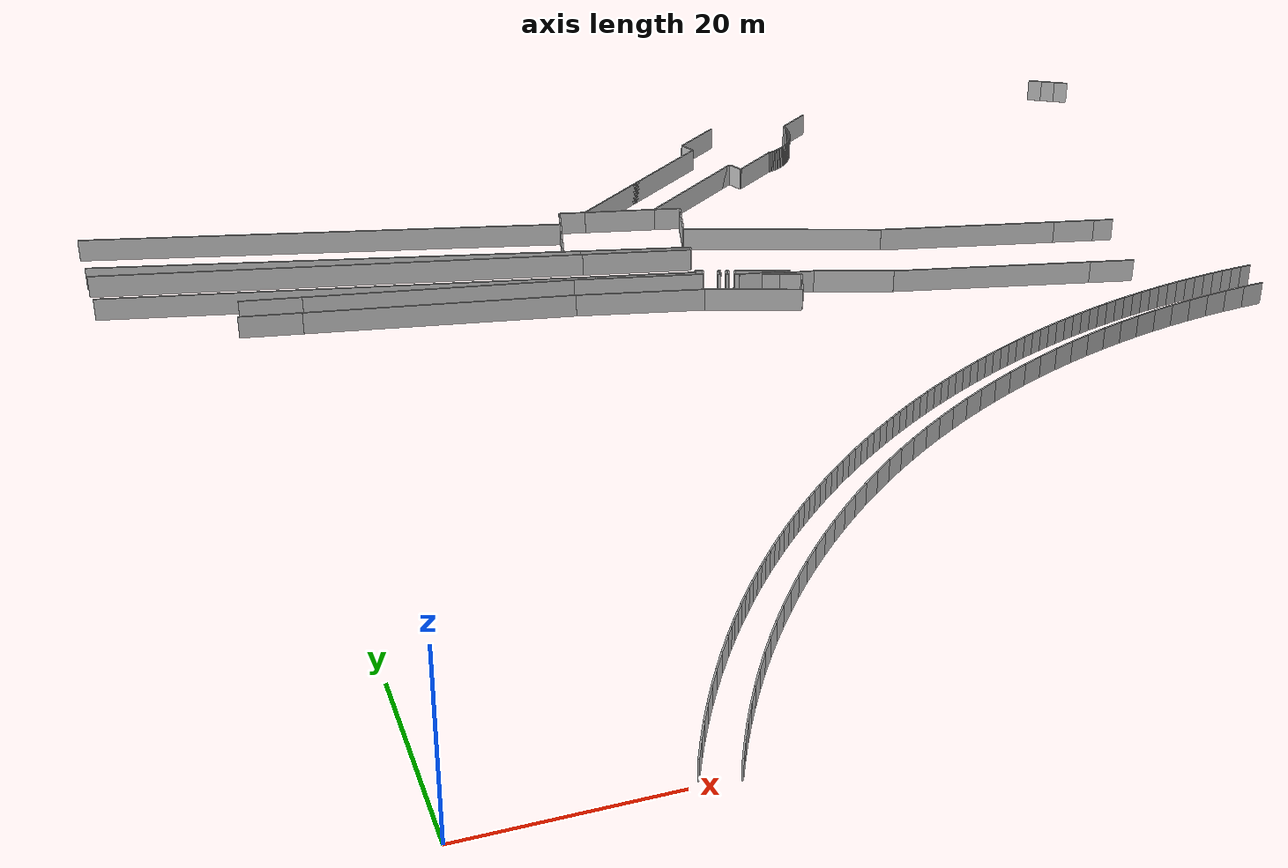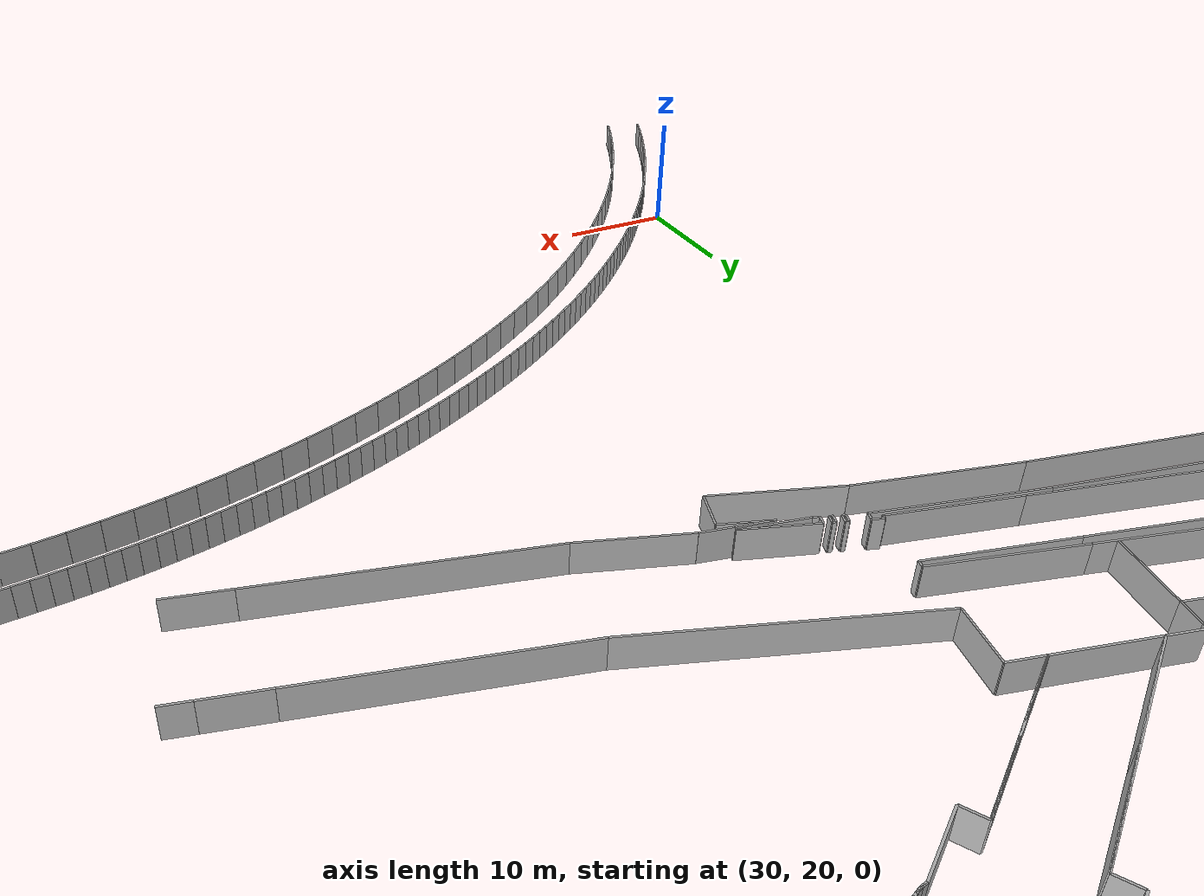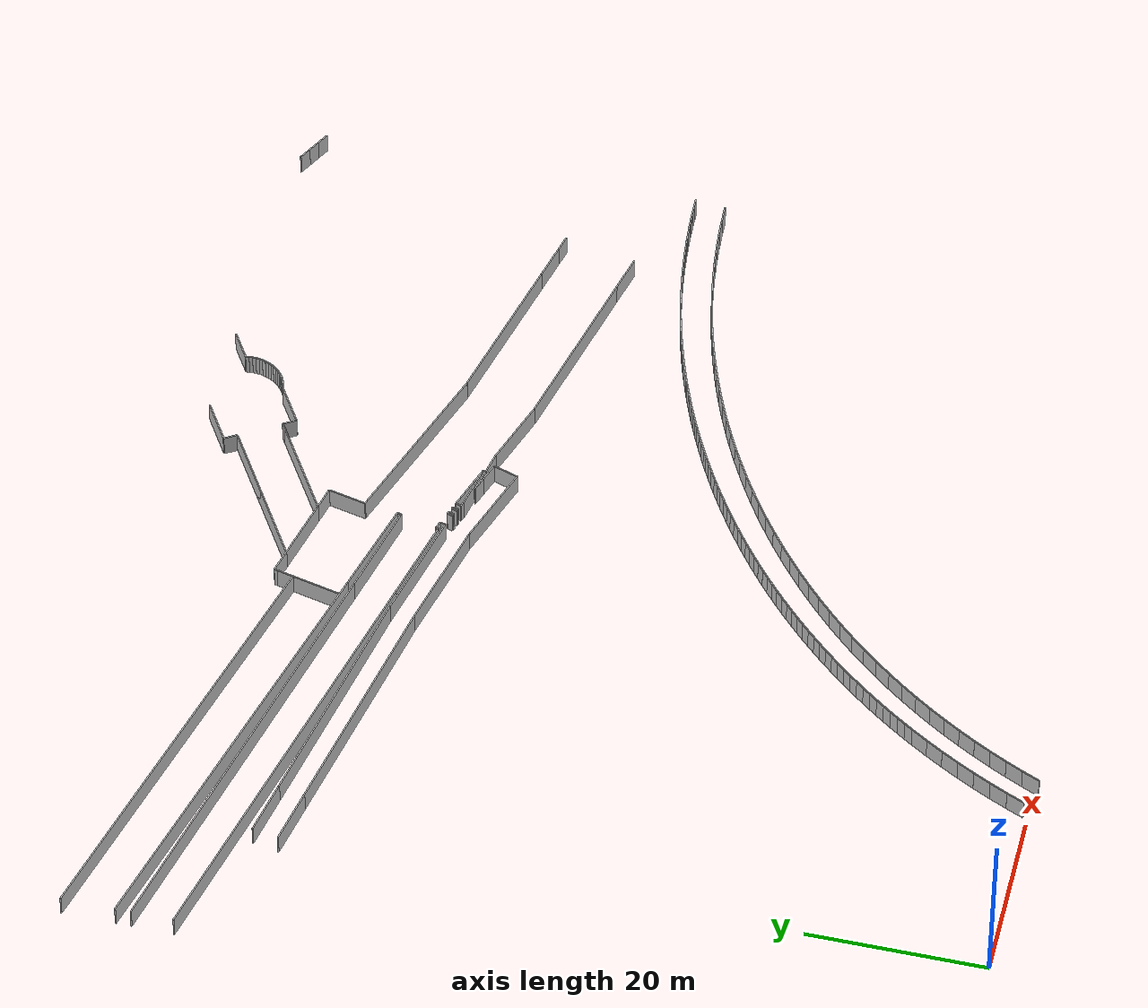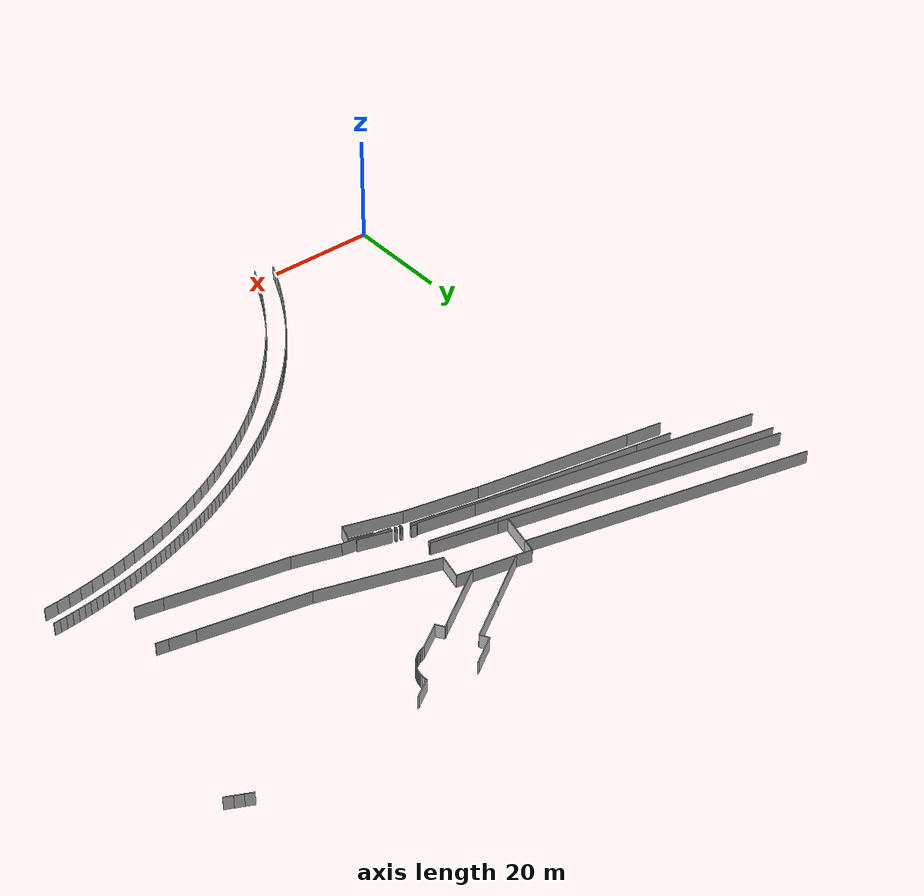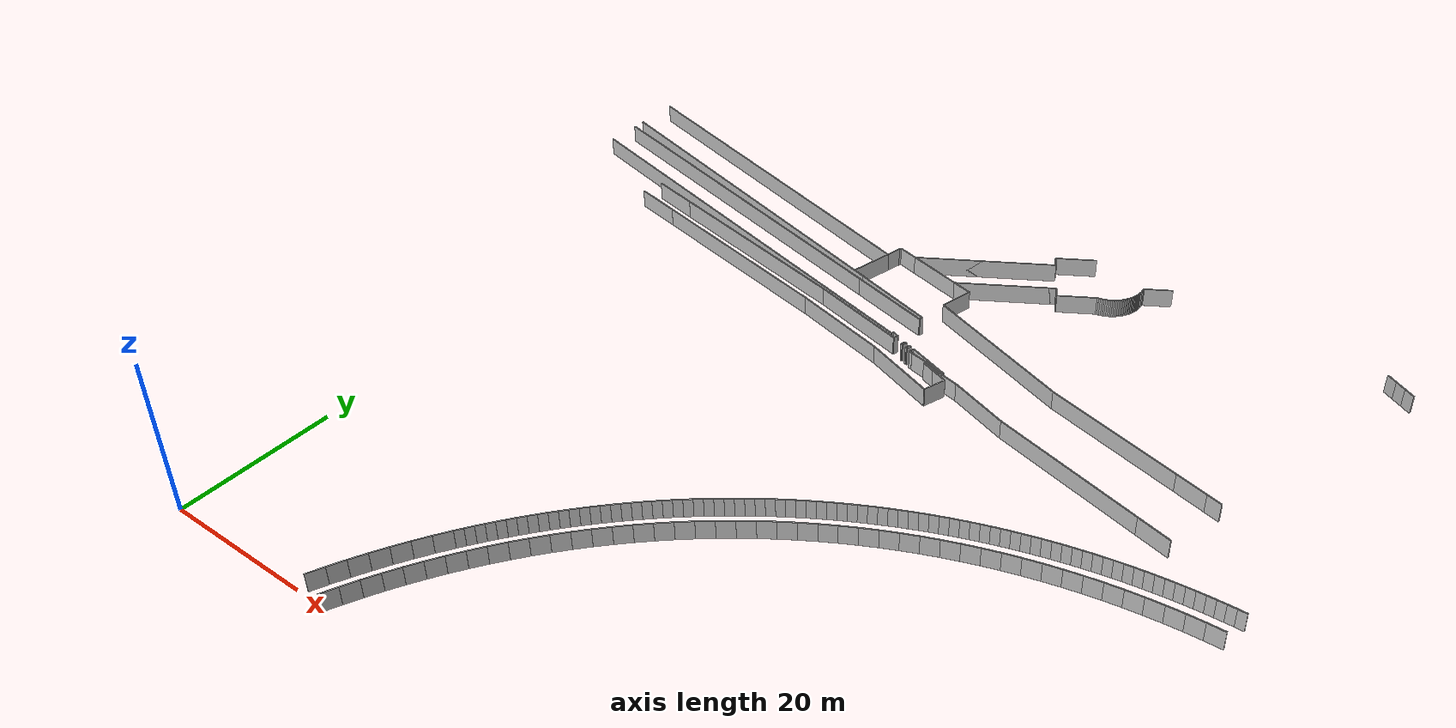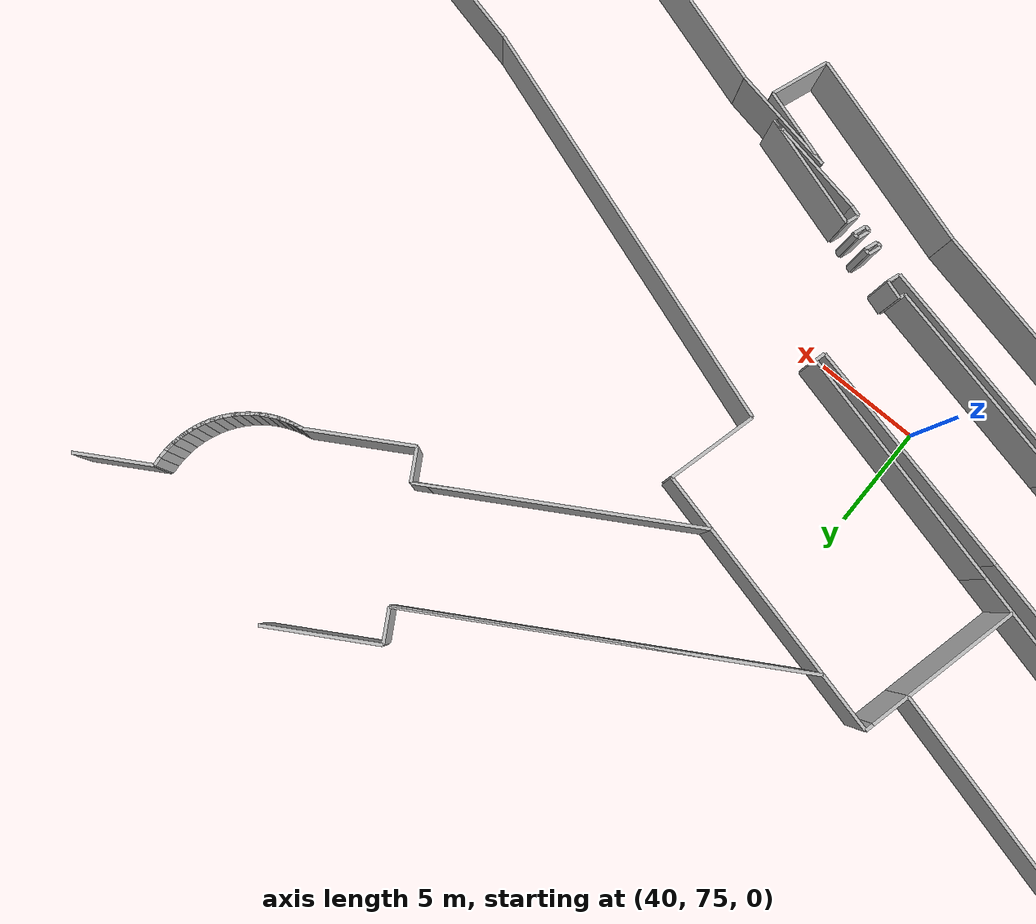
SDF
<?xml version="1.0" ?>
<sdf version="1.6">
  <model name="sps_0602">
    <pose frame="">0 0 0 0 -0 0</pose>
    <static>1</static>
    <self_collide>0</self_collide>
    <allow_auto_disable>0</allow_auto_disable>
    <link name="Wall9">
      <kinematic>0</kinematic>
      <gravity>1</gravity>
      <self_collide>0</self_collide>
      <collision name="collision">
        <geometry>
          <box>
            <size>2.75977 0.15 2.5</size>
          </box>
        </geometry>
        <pose frame="">0 0 0 0 -0 0</pose>
      </collision>
      <visual name="visual">
        <geometry>
          <box>
            <size>2.75977 0.15 2.5</size>
          </box>
        </geometry>
        <pose frame="">0 0 0 0 -0 0</pose>
        <cast_shadows>1</cast_shadows>
        <transparency>0.0</transparency>
      </visual>
      <pose frame="">35.9014 86.7282 1.25 0 -0 2.9133</pose>
    </link>
    <link name="Wall10">
      <kinematic>0</kinematic>
      <gravity>1</gravity>
      <self_collide>0</self_collide>
      <collision name="collision">
        <geometry>
          <box>
            <size>0.636607 0.15 2.5</size>
          </box>
        </geometry>
        <pose frame="">0 0 0 0 -0 0</pose>
      </collision>
      <visual name="visual">
        <geometry>
          <box>
            <size>0.636607 0.15 2.5</size>
          </box>
        </geometry>
        <pose frame="">0 0 0 0 -0 0</pose>
        <cast_shadows>1</cast_shadows>
        <transparency>0.0</transparency>
      </visual>
      <pose frame="">45.3445 70.6797 1.25 0 -0 1.2512</pose>
    </link>
    <link name="Wall11">
      <kinematic>0</kinematic>
      <gravity>1</gravity>
      <self_collide>0</self_collide>
      <collision name="collision">
        <geometry>
          <box>
            <size>0.892807 0.15 2.5</size>
          </box>
        </geometry>
        <pose frame="">0 0 0 0 -0 0</pose>
      </collision>
      <visual name="visual">
        <geometry>
          <box>
            <size>0.892807 0.15 2.5</size>
          </box>
        </geometry>
        <pose frame="">0 0 0 0 -0 0</pose>
        <cast_shadows>1</cast_shadows>
        <transparency>0.0</transparency>
      </visual>
      <pose frame="">45.0201 71.1203 1.25 0 0 -0.315222</pose>
    </link>
    <link name="Wall12">
      <kinematic>0</kinematic>
      <gravity>1</gravity>
      <self_collide>0</self_collide>
      <collision name="collision">
        <geometry>
          <box>
            <size>0.270044 0.15 2.5</size>
          </box>
        </geometry>
        <pose frame="">0 0 0 0 -0 0</pose>
      </collision>
      <visual name="visual">
        <geometry>
          <box>
            <size>0.270044 0.15 2.5</size>
          </box>
        </geometry>
        <pose frame="">0 0 0 0 -0 0</pose>
        <cast_shadows>1</cast_shadows>
        <transparency>0.0</transparency>
      </visual>
      <pose frame="">46.7982 69.8634 1.25 0 -0 2.82463</pose>
    </link>
    <link name="Wall13">
      <kinematic>0</kinematic>
      <gravity>1</gravity>
      <self_collide>0</self_collide>
      <collision name="collision">
        <geometry>
          <box>
            <size>4.45016 0.15 2.5</size>
          </box>
        </geometry>
        <pose frame="">0 0 0 0 -0 0</pose>
      </collision>
      <visual name="visual">
        <geometry>
          <box>
            <size>4.45016 0.15 2.5</size>
          </box>
        </geometry>
        <pose frame="">0 0 0 0 -0 0</pose>
        <cast_shadows>1</cast_shadows>
        <transparency>0.0</transparency>
      </visual>
      <pose frame="">46.7163 81.9306 1.25 0 0 -1.79919</pose>
    </link>
    <link name="Wall14">
      <kinematic>0</kinematic>
      <gravity>1</gravity>
      <self_collide>0</self_collide>
      <collision name="collision">
        <geometry>
          <box>
            <size>0.646784 0.15 2.5</size>
          </box>
        </geometry>
        <pose frame="">0 0 0 0 -0 0</pose>
      </collision>
      <visual name="visual">
        <geometry>
          <box>
            <size>0.646784 0.15 2.5</size>
          </box>
        </geometry>
        <pose frame="">0 0 0 0 -0 0</pose>
        <cast_shadows>1</cast_shadows>
        <transparency>0.0</transparency>
      </visual>
      <pose frame="">47.5969 69.9398 1.25 0 -0 1.25382</pose>
    </link>
    <link name="Wall15">
      <kinematic>0</kinematic>
      <gravity>1</gravity>
      <self_collide>0</self_collide>
      <collision name="collision">
        <geometry>
          <box>
            <size>0.26993 0.15 2.5</size>
          </box>
        </geometry>
        <pose frame="">0 0 0 0 -0 0</pose>
      </collision>
      <visual name="visual">
        <geometry>
          <box>
            <size>0.26993 0.15 2.5</size>
          </box>
        </geometry>
        <pose frame="">0 0 0 0 -0 0</pose>
        <cast_shadows>1</cast_shadows>
        <transparency>0.0</transparency>
      </visual>
      <pose frame="">47.8259 70.2052 1.25 0 0 -0.315673</pose>
    </link>
    <link name="Wall16">
      <kinematic>0</kinematic>
      <gravity>1</gravity>
      <self_collide>0</self_collide>
      <collision name="collision">
        <geometry>
          <box>
            <size>0.649519 0.15 2.5</size>
          </box>
        </geometry>
        <pose frame="">0 0 0 0 -0 0</pose>
      </collision>
      <visual name="visual">
        <geometry>
          <box>
            <size>0.649519 0.15 2.5</size>
          </box>
        </geometry>
        <pose frame="">0 0 0 0 -0 0</pose>
        <cast_shadows>1</cast_shadows>
        <transparency>0.0</transparency>
      </visual>
      <pose frame="">48.4228 69.6688 1.25 0 -0 1.25095</pose>
    </link>
    <link name="Wall17">
      <kinematic>0</kinematic>
      <gravity>1</gravity>
      <self_collide>0</self_collide>
      <collision name="collision">
        <geometry>
          <box>
            <size>18.3065 0.15 2.5</size>
          </box>
        </geometry>
        <pose frame="">0 0 0 0 -0 0</pose>
      </collision>
      <visual name="visual">
        <geometry>
          <box>
            <size>18.3065 0.15 2.5</size>
          </box>
        </geometry>
        <pose frame="">0 0 0 0 -0 0</pose>
        <cast_shadows>1</cast_shadows>
        <transparency>0.0</transparency>
      </visual>
      <pose frame="">45.0148 91.2553 1.25 0 0 -2.58452</pose>
    </link>
    <link name="Wall102">
      <kinematic>0</kinematic>
      <gravity>1</gravity>
      <self_collide>0</self_collide>
      <collision name="collision">
        <geometry>
          <box>
            <size>0.299763 0.15 2.5</size>
          </box>
        </geometry>
        <pose frame="">0 0 0 0 -0 0</pose>
      </collision>
      <visual name="visual">
        <geometry>
          <box>
            <size>0.299763 0.15 2.5</size>
          </box>
        </geometry>
        <pose frame="">0 0 0 0 -0 0</pose>
        <cast_shadows>1</cast_shadows>
        <transparency>0.0</transparency>
      </visual>
      <pose frame="">44.5618 71.1127 1.25 0 0 -1.79898</pose>
    </link>
    <link name="Wall106">
      <kinematic>0</kinematic>
      <gravity>1</gravity>
      <self_collide>0</self_collide>
      <collision name="collision">
        <geometry>
          <box>
            <size>51.5639 0.15 2.5</size>
          </box>
        </geometry>
        <pose frame="">0 0 0 0 -0 0</pose>
      </collision>
      <visual name="visual">
        <geometry>
          <box>
            <size>51.5639 0.15 2.5</size>
          </box>
        </geometry>
        <pose frame="">0 0 0 0 -0 0</pose>
        <cast_shadows>1</cast_shadows>
        <transparency>0.0</transparency>
      </visual>
      <pose frame="">9.46944 85.0621 1.25 0 0 -0.246916</pose>
    </link>
    <link name="Wall107">
      <kinematic>0</kinematic>
      <gravity>1</gravity>
      <self_collide>0</self_collide>
      <collision name="collision">
        <geometry>
          <box>
            <size>11.5635 0.15 2.5</size>
          </box>
        </geometry>
        <pose frame="">0 0 0 0 -0 0</pose>
      </collision>
      <visual name="visual">
        <geometry>
          <box>
            <size>11.5635 0.15 2.5</size>
          </box>
        </geometry>
        <pose frame="">0 0 0 0 -0 0</pose>
        <cast_shadows>1</cast_shadows>
        <transparency>0.0</transparency>
      </visual>
      <pose frame="">40.0759 77.3474 1.25 0 0 -0.246916</pose>
    </link>
    <link name="Wall108">
      <kinematic>0</kinematic>
      <gravity>1</gravity>
      <self_collide>0</self_collide>
      <collision name="collision">
        <geometry>
          <box>
            <size>0.643851 0.15 2.5</size>
          </box>
        </geometry>
        <pose frame="">0 0 0 0 -0 0</pose>
      </collision>
      <visual name="visual">
        <geometry>
          <box>
            <size>0.643851 0.15 2.5</size>
          </box>
        </geometry>
        <pose frame="">0 0 0 0 -0 0</pose>
        <cast_shadows>1</cast_shadows>
        <transparency>0.0</transparency>
      </visual>
      <pose frame="">47.0268 70.1272 1.25 0 -0 1.25402</pose>
    </link>
    <link name="Wall109">
      <kinematic>0</kinematic>
      <gravity>1</gravity>
      <self_collide>0</self_collide>
      <collision name="collision">
        <geometry>
          <box>
            <size>0.269889 0.15 2.5</size>
          </box>
        </geometry>
        <pose frame="">0 0 0 0 -0 0</pose>
      </collision>
      <visual name="visual">
        <geometry>
          <box>
            <size>0.269889 0.15 2.5</size>
          </box>
        </geometry>
        <pose frame="">0 0 0 0 -0 0</pose>
        <cast_shadows>1</cast_shadows>
        <transparency>0.0</transparency>
      </visual>
      <pose frame="">47.6243 69.5904 1.25 0 -0 2.8242</pose>
    </link>
    <link name="Wall179">
      <kinematic>0</kinematic>
      <gravity>1</gravity>
      <self_collide>0</self_collide>
      <collision name="collision">
        <geometry>
          <box>
            <size>51.1342 0.15 2.5</size>
          </box>
        </geometry>
        <pose frame="">0 0 0 0 -0 0</pose>
      </collision>
      <visual name="visual">
        <geometry>
          <box>
            <size>51.1342 0.15 2.5</size>
          </box>
        </geometry>
        <pose frame="">0 0 0 0 -0 0</pose>
        <cast_shadows>1</cast_shadows>
        <transparency>0.0</transparency>
      </visual>
      <pose frame="">9.25314 91.0811 1.25 0 -0 2.89341</pose>
    </link>
    <link name="Wall183">
      <kinematic>0</kinematic>
      <gravity>1</gravity>
      <self_collide>0</self_collide>
      <collision name="collision">
        <geometry>
          <box>
            <size>0.388056 0.15 2.5</size>
          </box>
        </geometry>
        <pose frame="">0 0 0 0 -0 0</pose>
      </collision>
      <visual name="visual">
        <geometry>
          <box>
            <size>0.388056 0.15 2.5</size>
          </box>
        </geometry>
        <pose frame="">0 0 0 0 -0 0</pose>
        <cast_shadows>1</cast_shadows>
        <transparency>0.0</transparency>
      </visual>
      <pose frame="">34.5134 86.8515 1.25 0 0 -1.79911</pose>
    </link>
    <link name="Wall184">
      <kinematic>0</kinematic>
      <gravity>1</gravity>
      <self_collide>0</self_collide>
      <collision name="collision">
        <geometry>
          <box>
            <size>1.91142 0.15 2.5</size>
          </box>
        </geometry>
        <pose frame="">0 0 0 0 -0 0</pose>
      </collision>
      <visual name="visual">
        <geometry>
          <box>
            <size>1.91142 0.15 2.5</size>
          </box>
        </geometry>
        <pose frame="">0 0 0 0 -0 0</pose>
        <cast_shadows>1</cast_shadows>
        <transparency>0.0</transparency>
      </visual>
      <pose frame="">34.2531 85.7316 1.25 0 0 -1.79911</pose>
    </link>
    <link name="Wall185">
      <kinematic>0</kinematic>
      <gravity>1</gravity>
      <self_collide>0</self_collide>
      <collision name="collision">
        <geometry>
          <box>
            <size>0.500124 0.15 2.5</size>
          </box>
        </geometry>
        <pose frame="">0 0 0 0 -0 0</pose>
      </collision>
      <visual name="visual">
        <geometry>
          <box>
            <size>0.500124 0.15 2.5</size>
          </box>
        </geometry>
        <pose frame="">0 0 0 0 -0 0</pose>
        <cast_shadows>1</cast_shadows>
        <transparency>0.0</transparency>
      </visual>
      <pose frame="">45.6258 75.6907 1.25 0 0 -1.79878</pose>
    </link>
    <link name="Wall186">
      <kinematic>0</kinematic>
      <gravity>1</gravity>
      <self_collide>0</self_collide>
      <collision name="collision">
        <geometry>
          <box>
            <size>2.74025 0.15 2.5</size>
          </box>
        </geometry>
        <pose frame="">0 0 0 0 -0 0</pose>
      </collision>
      <visual name="visual">
        <geometry>
          <box>
            <size>2.74025 0.15 2.5</size>
          </box>
        </geometry>
        <pose frame="">0 0 0 0 -0 0</pose>
        <cast_shadows>1</cast_shadows>
        <transparency>0.0</transparency>
      </visual>
      <pose frame="">45.8856 84.4083 1.25 0 0 -0.228528</pose>
    </link>
    <link name="Wall187">
      <kinematic>0</kinematic>
      <gravity>1</gravity>
      <self_collide>0</self_collide>
      <collision name="collision">
        <geometry>
          <box>
            <size>5.337 0.15 2.5</size>
          </box>
        </geometry>
        <pose frame="">0 0 0 0 -0 0</pose>
      </collision>
      <visual name="visual">
        <geometry>
          <box>
            <size>5.337 0.15 2.5</size>
          </box>
        </geometry>
        <pose frame="">0 0 0 0 -0 0</pose>
        <cast_shadows>1</cast_shadows>
        <transparency>0.0</transparency>
      </visual>
      <pose frame="">51.4278 68.6879 1.25 0 0 -0.19276</pose>
    </link>
    <link name="Wall188">
      <kinematic>0</kinematic>
      <gravity>1</gravity>
      <self_collide>0</self_collide>
      <collision name="collision">
        <geometry>
          <box>
            <size>5.80805 0.15 2.5</size>
          </box>
        </geometry>
        <pose frame="">0 0 0 0 -0 0</pose>
      </collision>
      <visual name="visual">
        <geometry>
          <box>
            <size>5.80805 0.15 2.5</size>
          </box>
        </geometry>
        <pose frame="">0 0 0 0 -0 0</pose>
        <cast_shadows>1</cast_shadows>
        <transparency>0.0</transparency>
      </visual>
      <pose frame="">51.2858 69.0769 1.25 0 0 -0.315167</pose>
    </link>
    <link name="Wall276">
      <kinematic>0</kinematic>
      <gravity>1</gravity>
      <self_collide>0</self_collide>
      <collision name="collision">
        <geometry>
          <box>
            <size>0.514026 0.15 2.5</size>
          </box>
        </geometry>
        <pose frame="">0 0 0 0 -0 0</pose>
      </collision>
      <visual name="visual">
        <geometry>
          <box>
            <size>0.514026 0.15 2.5</size>
          </box>
        </geometry>
        <pose frame="">0 0 0 0 -0 0</pose>
        <cast_shadows>1</cast_shadows>
        <transparency>0.0</transparency>
      </visual>
      <pose frame="">48.5647 69.2798 1.25 0 0 -0.319347</pose>
    </link>
    <link name="Wall339">
      <kinematic>0</kinematic>
      <gravity>1</gravity>
      <self_collide>0</self_collide>
      <collision name="collision">
        <geometry>
          <box>
            <size>11.3954 0.15 2.5</size>
          </box>
        </geometry>
        <pose frame="">0 0 0 0 -0 0</pose>
      </collision>
      <visual name="visual">
        <geometry>
          <box>
            <size>11.3954 0.15 2.5</size>
          </box>
        </geometry>
        <pose frame="">0 0 0 0 -0 0</pose>
        <cast_shadows>1</cast_shadows>
        <transparency>0.0</transparency>
      </visual>
      <pose frame="">40.0193 76.7364 1.25 0 -0 2.91334</pose>
    </link>
    <link name="Wall340">
      <kinematic>0</kinematic>
      <gravity>1</gravity>
      <self_collide>0</self_collide>
      <collision name="collision">
        <geometry>
          <box>
            <size>51.3314 0.15 2.5</size>
          </box>
        </geometry>
        <pose frame="">0 0 0 0 -0 0</pose>
      </collision>
      <visual name="visual">
        <geometry>
          <box>
            <size>51.3314 0.15 2.5</size>
          </box>
        </geometry>
        <pose frame="">0 0 0 0 -0 0</pose>
        <cast_shadows>1</cast_shadows>
        <transparency>0.0</transparency>
      </visual>
      <pose frame="">9.46944 83.8332 1.25 0 -0 2.91334</pose>
    </link>
    <link name="Wall343">
      <kinematic>0</kinematic>
      <gravity>1</gravity>
      <self_collide>0</self_collide>
      <collision name="collision">
        <geometry>
          <box>
            <size>3.00012 0.15 2.5</size>
          </box>
        </geometry>
        <pose frame="">0 0 0 0 -0 0</pose>
      </collision>
      <visual name="visual">
        <geometry>
          <box>
            <size>3.00012 0.15 2.5</size>
          </box>
        </geometry>
        <pose frame="">0 0 0 0 -0 0</pose>
        <cast_shadows>1</cast_shadows>
        <transparency>0.0</transparency>
      </visual>
      <pose frame="">54.4389 65.7577 1.25 0 0 -1.89019</pose>
    </link>
    <link name="Wall344">
      <kinematic>0</kinematic>
      <gravity>1</gravity>
      <self_collide>0</self_collide>
      <collision name="collision">
        <geometry>
          <box>
            <size>1.78351 0.15 2.5</size>
          </box>
        </geometry>
        <pose frame="">0 0 0 0 -0 0</pose>
      </collision>
      <visual name="visual">
        <geometry>
          <box>
            <size>1.78351 0.15 2.5</size>
          </box>
        </geometry>
        <pose frame="">0 0 0 0 -0 0</pose>
        <cast_shadows>1</cast_shadows>
        <transparency>0.0</transparency>
      </visual>
      <pose frame="">51.912 68.173 1.25 0 0 -0.319281</pose>
    </link>
    <link name="Wall345">
      <kinematic>0</kinematic>
      <gravity>1</gravity>
      <self_collide>0</self_collide>
      <collision name="collision">
        <geometry>
          <box>
            <size>2.26574 0.15 2.5</size>
          </box>
        </geometry>
        <pose frame="">0 0 0 0 -0 0</pose>
      </collision>
      <visual name="visual">
        <geometry>
          <box>
            <size>2.26574 0.15 2.5</size>
          </box>
        </geometry>
        <pose frame="">0 0 0 0 -0 0</pose>
        <cast_shadows>1</cast_shadows>
        <transparency>0.0</transparency>
      </visual>
      <pose frame="">53.8343 67.5375 1.25 0 0 -0.319281</pose>
    </link>
    <link name="Wall423">
      <kinematic>0</kinematic>
      <gravity>1</gravity>
      <self_collide>0</self_collide>
      <collision name="collision">
        <geometry>
          <box>
            <size>0.643271 0.15 2.5</size>
          </box>
        </geometry>
        <pose frame="">0 0 0 0 -0 0</pose>
      </collision>
      <visual name="visual">
        <geometry>
          <box>
            <size>0.643271 0.15 2.5</size>
          </box>
        </geometry>
        <pose frame="">0 0 0 0 -0 0</pose>
        <cast_shadows>1</cast_shadows>
        <transparency>0.0</transparency>
      </visual>
      <pose frame="">46.7702 70.2111 1.25 0 -0 1.25373</pose>
    </link>
    <link name="Wall424">
      <kinematic>0</kinematic>
      <gravity>1</gravity>
      <self_collide>0</self_collide>
      <collision name="collision">
        <geometry>
          <box>
            <size>0.269854 0.15 2.5</size>
          </box>
        </geometry>
        <pose frame="">0 0 0 0 -0 0</pose>
      </collision>
      <visual name="visual">
        <geometry>
          <box>
            <size>0.269854 0.15 2.5</size>
          </box>
        </geometry>
        <pose frame="">0 0 0 0 -0 0</pose>
        <cast_shadows>1</cast_shadows>
        <transparency>0.0</transparency>
      </visual>
      <pose frame="">46.9987 70.4749 1.25 0 0 -0.314813</pose>
    </link>
    <link name="Wall425">
      <kinematic>0</kinematic>
      <gravity>1</gravity>
      <self_collide>0</self_collide>
      <collision name="collision">
        <geometry>
          <box>
            <size>2.92208 0.15 2.5</size>
          </box>
        </geometry>
        <pose frame="">0 0 0 0 -0 0</pose>
      </collision>
      <visual name="visual">
        <geometry>
          <box>
            <size>2.92208 0.15 2.5</size>
          </box>
        </geometry>
        <pose frame="">0 0 0 0 -0 0</pose>
        <cast_shadows>1</cast_shadows>
        <transparency>0.0</transparency>
      </visual>
      <pose frame="">52.4992 68.173 1.25 0 0 -0.192773</pose>
    </link>
    <link name="Wall426">
      <kinematic>0</kinematic>
      <gravity>1</gravity>
      <self_collide>0</self_collide>
      <collision name="collision">
        <geometry>
          <box>
            <size>2.49485 0.15 2.5</size>
          </box>
        </geometry>
        <pose frame="">0 0 0 0 -0 0</pose>
      </collision>
      <visual name="visual">
        <geometry>
          <box>
            <size>2.49485 0.15 2.5</size>
          </box>
        </geometry>
        <pose frame="">0 0 0 0 -0 0</pose>
        <cast_shadows>1</cast_shadows>
        <transparency>0.0</transparency>
      </visual>
      <pose frame="">55.1575 67.6541 1.25 0 0 -0.192773</pose>
    </link>
    <link name="Wall512">
      <kinematic>0</kinematic>
      <gravity>1</gravity>
      <self_collide>0</self_collide>
      <collision name="collision">
        <geometry>
          <box>
            <size>10.3277 0.15 2.5</size>
          </box>
        </geometry>
        <pose frame="">0 0 0 0 -0 0</pose>
      </collision>
      <visual name="visual">
        <geometry>
          <box>
            <size>10.3277 0.15 2.5</size>
          </box>
        </geometry>
        <pose frame="">0 0 0 0 -0 0</pose>
        <cast_shadows>1</cast_shadows>
        <transparency>0.0</transparency>
      </visual>
      <pose frame="">39.4986 72.1382 1.25 0 -0 2.91274</pose>
    </link>
    <link name="Wall513">
      <kinematic>0</kinematic>
      <gravity>1</gravity>
      <self_collide>0</self_collide>
      <collision name="collision">
        <geometry>
          <box>
            <size>51.3386 0.15 2.5</size>
          </box>
        </geometry>
        <pose frame="">0 0 0 0 -0 0</pose>
      </collision>
      <visual name="visual">
        <geometry>
          <box>
            <size>51.3386 0.15 2.5</size>
          </box>
        </geometry>
        <pose frame="">0 0 0 0 -0 0</pose>
        <cast_shadows>1</cast_shadows>
        <transparency>0.0</transparency>
      </visual>
      <pose frame="">9.46944 79.133 1.25 0 -0 2.91274</pose>
    </link>
    <link name="Wall516">
      <kinematic>0</kinematic>
      <gravity>1</gravity>
      <self_collide>0</self_collide>
      <collision name="collision">
        <geometry>
          <box>
            <size>0.647247 0.15 2.5</size>
          </box>
        </geometry>
        <pose frame="">0 0 0 0 -0 0</pose>
      </collision>
      <visual name="visual">
        <geometry>
          <box>
            <size>0.647247 0.15 2.5</size>
          </box>
        </geometry>
        <pose frame="">0 0 0 0 -0 0</pose>
        <cast_shadows>1</cast_shadows>
        <transparency>0.0</transparency>
      </visual>
      <pose frame="">47.8534 69.8558 1.25 0 -0 1.25376</pose>
    </link>
    <link name="Wall517">
      <kinematic>0</kinematic>
      <gravity>1</gravity>
      <self_collide>0</self_collide>
      <collision name="collision">
        <geometry>
          <box>
            <size>13.0031 0.15 2.5</size>
          </box>
        </geometry>
        <pose frame="">0 0 0 0 -0 0</pose>
      </collision>
      <visual name="visual">
        <geometry>
          <box>
            <size>13.0031 0.15 2.5</size>
          </box>
        </geometry>
        <pose frame="">0 0 0 0 -0 0</pose>
        <cast_shadows>1</cast_shadows>
        <transparency>0.0</transparency>
      </visual>
      <pose frame="">50.0687 88.1576 1.25 0 0 -2.58425</pose>
    </link>
    <link name="Wall518">
      <kinematic>0</kinematic>
      <gravity>1</gravity>
      <self_collide>0</self_collide>
      <collision name="collision">
        <geometry>
          <box>
            <size>21.0684 0.15 2.5</size>
          </box>
        </geometry>
        <pose frame="">0 0 0 0 -0 0</pose>
      </collision>
      <visual name="visual">
        <geometry>
          <box>
            <size>21.0684 0.15 2.5</size>
          </box>
        </geometry>
        <pose frame="">0 0 0 0 -0 0</pose>
        <cast_shadows>1</cast_shadows>
        <transparency>0.0</transparency>
      </visual>
      <pose frame="">56.209 76.4408 1.25 0 -0 2.82071</pose>
    </link>
    <link name="Wall519">
      <kinematic>0</kinematic>
      <gravity>1</gravity>
      <self_collide>0</self_collide>
      <collision name="collision">
        <geometry>
          <box>
            <size>20.7242 0.15 2.5</size>
          </box>
        </geometry>
        <pose frame="">0 0 0 0 -0 0</pose>
      </collision>
      <visual name="visual">
        <geometry>
          <box>
            <size>20.7242 0.15 2.5</size>
          </box>
        </geometry>
        <pose frame="">0 0 0 0 -0 0</pose>
        <cast_shadows>1</cast_shadows>
        <transparency>0.0</transparency>
      </visual>
      <pose frame="">74.3761 62.4944 1.25 0 0 -0.22823</pose>
    </link>
    <link name="Wall520">
      <kinematic>0</kinematic>
      <gravity>1</gravity>
      <self_collide>0</self_collide>
      <collision name="collision">
        <geometry>
          <box>
            <size>4.60319 0.15 2.5</size>
          </box>
        </geometry>
        <pose frame="">0 0 0 0 -0 0</pose>
      </collision>
      <visual name="visual">
        <geometry>
          <box>
            <size>4.60319 0.15 2.5</size>
          </box>
        </geometry>
        <pose frame="">0 0 0 0 -0 0</pose>
        <cast_shadows>1</cast_shadows>
        <transparency>0.0</transparency>
      </visual>
      <pose frame="">86.7114 59.6292 1.25 0 0 -0.22823</pose>
    </link>
    <link name="Wall597">
      <kinematic>0</kinematic>
      <gravity>1</gravity>
      <self_collide>0</self_collide>
      <collision name="collision">
        <geometry>
          <box>
            <size>10.0429 0.15 2.5</size>
          </box>
        </geometry>
        <pose frame="">0 0 0 0 -0 0</pose>
      </collision>
      <visual name="visual">
        <geometry>
          <box>
            <size>10.0429 0.15 2.5</size>
          </box>
        </geometry>
        <pose frame="">0 0 0 0 -0 0</pose>
        <cast_shadows>1</cast_shadows>
        <transparency>0.0</transparency>
      </visual>
      <pose frame="">49.2002 65.9099 1.25 0 0 -0.319329</pose>
    </link>
    <link name="Wall598">
      <kinematic>0</kinematic>
      <gravity>1</gravity>
      <self_collide>0</self_collide>
      <collision name="collision">
        <geometry>
          <box>
            <size>8.31023 0.15 2.5</size>
          </box>
        </geometry>
        <pose frame="">0 0 0 0 -0 0</pose>
      </collision>
      <visual name="visual">
        <geometry>
          <box>
            <size>8.31023 0.15 2.5</size>
          </box>
        </geometry>
        <pose frame="">0 0 0 0 -0 0</pose>
        <cast_shadows>1</cast_shadows>
        <transparency>0.0</transparency>
      </visual>
      <pose frame="">60.3323 66.127 1.25 0 0 -0.315201</pose>
    </link>
    <link name="Wall602">
      <kinematic>0</kinematic>
      <gravity>1</gravity>
      <self_collide>0</self_collide>
      <collision name="collision">
        <geometry>
          <box>
            <size>2.02963 0.15 2.5</size>
          </box>
        </geometry>
        <pose frame="">0 0 0 0 -0 0</pose>
      </collision>
      <visual name="visual">
        <geometry>
          <box>
            <size>2.02963 0.15 2.5</size>
          </box>
        </geometry>
        <pose frame="">0 0 0 0 -0 0</pose>
        <cast_shadows>1</cast_shadows>
        <transparency>0.0</transparency>
      </visual>
      <pose frame="">89.6792 67.6634 1.25 0 -0 2.91326</pose>
    </link>
    <link name="Wall603">
      <kinematic>0</kinematic>
      <gravity>1</gravity>
      <self_collide>0</self_collide>
      <collision name="collision">
        <geometry>
          <box>
            <size>4.33377 0.15 2.5</size>
          </box>
        </geometry>
        <pose frame="">0 0 0 0 -0 0</pose>
      </collision>
      <visual name="visual">
        <geometry>
          <box>
            <size>4.33377 0.15 2.5</size>
          </box>
        </geometry>
        <pose frame="">0 0 0 0 -0 0</pose>
        <cast_shadows>1</cast_shadows>
        <transparency>0.0</transparency>
      </visual>
      <pose frame="">86.5801 68.3836 1.25 0 -0 2.91326</pose>
    </link>
    <link name="Wall604">
      <kinematic>0</kinematic>
      <gravity>1</gravity>
      <self_collide>0</self_collide>
      <collision name="collision">
        <geometry>
          <box>
            <size>18.7506 0.15 2.5</size>
          </box>
        </geometry>
        <pose frame="">0 0 0 0 -0 0</pose>
      </collision>
      <visual name="visual">
        <geometry>
          <box>
            <size>18.7506 0.15 2.5</size>
          </box>
        </geometry>
        <pose frame="">0 0 0 0 -0 0</pose>
        <cast_shadows>1</cast_shadows>
        <transparency>0.0</transparency>
      </visual>
      <pose frame="">75.3375 70.9962 1.25 0 -0 2.91326</pose>
    </link>
    <link name="Wall1408">
      <kinematic>0</kinematic>
      <gravity>1</gravity>
      <self_collide>0</self_collide>
      <collision name="collision">
        <geometry>
          <box>
            <size>5.75188 0.15 2.5</size>
          </box>
        </geometry>
        <pose frame="">0 0 0 0 -0 0</pose>
      </collision>
      <visual name="visual">
        <geometry>
          <box>
            <size>5.75188 0.15 2.5</size>
          </box>
        </geometry>
        <pose frame="">0 0 0 0 -0 0</pose>
        <cast_shadows>1</cast_shadows>
        <transparency>0.0</transparency>
      </visual>
      <pose frame="">33.3863 81.9993 1.25 0 0 -1.79898</pose>
    </link>
    <link name="Wall1639">
      <kinematic>0</kinematic>
      <gravity>1</gravity>
      <self_collide>0</self_collide>
      <collision name="collision">
        <geometry>
          <box>
            <size>2.22094 0.15 2.5</size>
          </box>
        </geometry>
        <pose frame="">0 0 0 0 -0 0</pose>
      </collision>
      <visual name="visual">
        <geometry>
          <box>
            <size>2.22094 0.15 2.5</size>
          </box>
        </geometry>
        <pose frame="">0 0 0 0 -0 0</pose>
        <cast_shadows>1</cast_shadows>
        <transparency>0.0</transparency>
      </visual>
      <pose frame="">21.4795 1.55992 1.25 0 -0 1.16072</pose>
    </link>
    <link name="Wall1640">
      <kinematic>0</kinematic>
      <gravity>1</gravity>
      <self_collide>0</self_collide>
      <collision name="collision">
        <geometry>
          <box>
            <size>2.22094 0.15 2.5</size>
          </box>
        </geometry>
        <pose frame="">0 0 0 0 -0 0</pose>
      </collision>
      <visual name="visual">
        <geometry>
          <box>
            <size>2.22094 0.15 2.5</size>
          </box>
        </geometry>
        <pose frame="">0 0 0 0 -0 0</pose>
        <cast_shadows>1</cast_shadows>
        <transparency>0.0</transparency>
      </visual>
      <pose frame="">22.3906 3.58522 1.25 0 -0 1.13547</pose>
    </link>
    <link name="Wall1641">
      <kinematic>0</kinematic>
      <gravity>1</gravity>
      <self_collide>0</self_collide>
      <collision name="collision">
        <geometry>
          <box>
            <size>2.22085 0.15 2.5</size>
          </box>
        </geometry>
        <pose frame="">0 0 0 0 -0 0</pose>
      </collision>
      <visual name="visual">
        <geometry>
          <box>
            <size>2.22085 0.15 2.5</size>
          </box>
        </geometry>
        <pose frame="">0 0 0 0 -0 0</pose>
        <cast_shadows>1</cast_shadows>
        <transparency>0.0</transparency>
      </visual>
      <pose frame="">23.3524 5.58681 1.25 0 -0 1.11017</pose>
    </link>
    <link name="Wall1642">
      <kinematic>0</kinematic>
      <gravity>1</gravity>
      <self_collide>0</self_collide>
      <collision name="collision">
        <geometry>
          <box>
            <size>2.2209 0.15 2.5</size>
          </box>
        </geometry>
        <pose frame="">0 0 0 0 -0 0</pose>
      </collision>
      <visual name="visual">
        <geometry>
          <box>
            <size>2.2209 0.15 2.5</size>
          </box>
        </geometry>
        <pose frame="">0 0 0 0 -0 0</pose>
        <cast_shadows>1</cast_shadows>
        <transparency>0.0</transparency>
      </visual>
      <pose frame="">24.3646 7.5634 1.25 0 -0 1.08486</pose>
    </link>
    <link name="Wall1643">
      <kinematic>0</kinematic>
      <gravity>1</gravity>
      <self_collide>0</self_collide>
      <collision name="collision">
        <geometry>
          <box>
            <size>2.22102 0.15 2.5</size>
          </box>
        </geometry>
        <pose frame="">0 0 0 0 -0 0</pose>
      </collision>
      <visual name="visual">
        <geometry>
          <box>
            <size>2.22102 0.15 2.5</size>
          </box>
        </geometry>
        <pose frame="">0 0 0 0 -0 0</pose>
        <cast_shadows>1</cast_shadows>
        <transparency>0.0</transparency>
      </visual>
      <pose frame="">25.4264 9.5139 1.25 0 -0 1.0597</pose>
    </link>
    <link name="Wall1644">
      <kinematic>0</kinematic>
      <gravity>1</gravity>
      <self_collide>0</self_collide>
      <collision name="collision">
        <geometry>
          <box>
            <size>2.22108 0.15 2.5</size>
          </box>
        </geometry>
        <pose frame="">0 0 0 0 -0 0</pose>
      </collision>
      <visual name="visual">
        <geometry>
          <box>
            <size>2.22108 0.15 2.5</size>
          </box>
        </geometry>
        <pose frame="">0 0 0 0 -0 0</pose>
        <cast_shadows>1</cast_shadows>
        <transparency>0.0</transparency>
      </visual>
      <pose frame="">26.5371 11.4371 1.25 0 -0 1.03443</pose>
    </link>
    <link name="Wall1645">
      <kinematic>0</kinematic>
      <gravity>1</gravity>
      <self_collide>0</self_collide>
      <collision name="collision">
        <geometry>
          <box>
            <size>2.22088 0.15 2.5</size>
          </box>
        </geometry>
        <pose frame="">0 0 0 0 -0 0</pose>
      </collision>
      <visual name="visual">
        <geometry>
          <box>
            <size>2.22088 0.15 2.5</size>
          </box>
        </geometry>
        <pose frame="">0 0 0 0 -0 0</pose>
        <cast_shadows>1</cast_shadows>
        <transparency>0.0</transparency>
      </visual>
      <pose frame="">27.6959 13.3316 1.25 0 -0 1.00925</pose>
    </link>
    <link name="Wall1646">
      <kinematic>0</kinematic>
      <gravity>1</gravity>
      <self_collide>0</self_collide>
      <collision name="collision">
        <geometry>
          <box>
            <size>1.11048 0.15 2.5</size>
          </box>
        </geometry>
        <pose frame="">0 0 0 0 -0 0</pose>
      </collision>
      <visual name="visual">
        <geometry>
          <box>
            <size>1.11048 0.15 2.5</size>
          </box>
        </geometry>
        <pose frame="">0 0 0 0 -0 0</pose>
        <cast_shadows>1</cast_shadows>
        <transparency>0.0</transparency>
      </visual>
      <pose frame="">28.5918 14.7358 1.25 0 -0 0.990324</pose>
    </link>
    <link name="Wall1647">
      <kinematic>0</kinematic>
      <gravity>1</gravity>
      <self_collide>0</self_collide>
      <collision name="collision">
        <geometry>
          <box>
            <size>1.11035 0.15 2.5</size>
          </box>
        </geometry>
        <pose frame="">0 0 0 0 -0 0</pose>
      </collision>
      <visual name="visual">
        <geometry>
          <box>
            <size>1.11035 0.15 2.5</size>
          </box>
        </geometry>
        <pose frame="">0 0 0 0 -0 0</pose>
        <cast_shadows>1</cast_shadows>
        <transparency>0.0</transparency>
      </visual>
      <pose frame="">29.2067 15.6604 1.25 0 -0 0.977503</pose>
    </link>
    <link name="Wall1648">
      <kinematic>0</kinematic>
      <gravity>1</gravity>
      <self_collide>0</self_collide>
      <collision name="collision">
        <geometry>
          <box>
            <size>1.11049 0.15 2.5</size>
          </box>
        </geometry>
        <pose frame="">0 0 0 0 -0 0</pose>
      </collision>
      <visual name="visual">
        <geometry>
          <box>
            <size>1.11049 0.15 2.5</size>
          </box>
        </geometry>
        <pose frame="">0 0 0 0 -0 0</pose>
        <cast_shadows>1</cast_shadows>
        <transparency>0.0</transparency>
      </visual>
      <pose frame="">29.8332 16.5771 1.25 0 -0 0.964942</pose>
    </link>
    <link name="Wall1649">
      <kinematic>0</kinematic>
      <gravity>1</gravity>
      <self_collide>0</self_collide>
      <collision name="collision">
        <geometry>
          <box>
            <size>1.1106 0.15 2.5</size>
          </box>
        </geometry>
        <pose frame="">0 0 0 0 -0 0</pose>
      </collision>
      <visual name="visual">
        <geometry>
          <box>
            <size>1.1106 0.15 2.5</size>
          </box>
        </geometry>
        <pose frame="">0 0 0 0 -0 0</pose>
        <cast_shadows>1</cast_shadows>
        <transparency>0.0</transparency>
      </visual>
      <pose frame="">30.4715 17.4859 1.25 0 -0 0.952182</pose>
    </link>
    <link name="Wall1650">
      <kinematic>0</kinematic>
      <gravity>1</gravity>
      <self_collide>0</self_collide>
      <collision name="collision">
        <geometry>
          <box>
            <size>1.11027 0.15 2.5</size>
          </box>
        </geometry>
        <pose frame="">0 0 0 0 -0 0</pose>
      </collision>
      <visual name="visual">
        <geometry>
          <box>
            <size>1.11027 0.15 2.5</size>
          </box>
        </geometry>
        <pose frame="">0 0 0 0 -0 0</pose>
        <cast_shadows>1</cast_shadows>
        <transparency>0.0</transparency>
      </visual>
      <pose frame="">31.1211 18.3865 1.25 0 -0 0.939632</pose>
    </link>
    <link name="Wall1651">
      <kinematic>0</kinematic>
      <gravity>1</gravity>
      <self_collide>0</self_collide>
      <collision name="collision">
        <geometry>
          <box>
            <size>1.11061 0.15 2.5</size>
          </box>
        </geometry>
        <pose frame="">0 0 0 0 -0 0</pose>
      </collision>
      <visual name="visual">
        <geometry>
          <box>
            <size>1.11061 0.15 2.5</size>
          </box>
        </geometry>
        <pose frame="">0 0 0 0 -0 0</pose>
        <cast_shadows>1</cast_shadows>
        <transparency>0.0</transparency>
      </visual>
      <pose frame="">31.7819 19.2789 1.25 0 -0 0.927207</pose>
    </link>
    <link name="Wall1652">
      <kinematic>0</kinematic>
      <gravity>1</gravity>
      <self_collide>0</self_collide>
      <collision name="collision">
        <geometry>
          <box>
            <size>1.11051 0.15 2.5</size>
          </box>
        </geometry>
        <pose frame="">0 0 0 0 -0 0</pose>
      </collision>
      <visual name="visual">
        <geometry>
          <box>
            <size>1.11051 0.15 2.5</size>
          </box>
        </geometry>
        <pose frame="">0 0 0 0 -0 0</pose>
        <cast_shadows>1</cast_shadows>
        <transparency>0.0</transparency>
      </visual>
      <pose frame="">32.4538 20.1631 1.25 0 -0 0.914786</pose>
    </link>
    <link name="Wall1653">
      <kinematic>0</kinematic>
      <gravity>1</gravity>
      <self_collide>0</self_collide>
      <collision name="collision">
        <geometry>
          <box>
            <size>1.11064 0.15 2.5</size>
          </box>
        </geometry>
        <pose frame="">0 0 0 0 -0 0</pose>
      </collision>
      <visual name="visual">
        <geometry>
          <box>
            <size>1.11064 0.15 2.5</size>
          </box>
        </geometry>
        <pose frame="">0 0 0 0 -0 0</pose>
        <cast_shadows>1</cast_shadows>
        <transparency>0.0</transparency>
      </visual>
      <pose frame="">33.1369 21.0387 1.25 0 -0 0.901771</pose>
    </link>
    <link name="Wall1654">
      <kinematic>0</kinematic>
      <gravity>1</gravity>
      <self_collide>0</self_collide>
      <collision name="collision">
        <geometry>
          <box>
            <size>1.11042 0.15 2.5</size>
          </box>
        </geometry>
        <pose frame="">0 0 0 0 -0 0</pose>
      </collision>
      <visual name="visual">
        <geometry>
          <box>
            <size>1.11042 0.15 2.5</size>
          </box>
        </geometry>
        <pose frame="">0 0 0 0 -0 0</pose>
        <cast_shadows>1</cast_shadows>
        <transparency>0.0</transparency>
      </visual>
      <pose frame="">33.8312 21.9054 1.25 0 -0 0.889008</pose>
    </link>
    <link name="Wall1655">
      <kinematic>0</kinematic>
      <gravity>1</gravity>
      <self_collide>0</self_collide>
      <collision name="collision">
        <geometry>
          <box>
            <size>1.11037 0.15 2.5</size>
          </box>
        </geometry>
        <pose frame="">0 0 0 0 -0 0</pose>
      </collision>
      <visual name="visual">
        <geometry>
          <box>
            <size>1.11037 0.15 2.5</size>
          </box>
        </geometry>
        <pose frame="">0 0 0 0 -0 0</pose>
        <cast_shadows>1</cast_shadows>
        <transparency>0.0</transparency>
      </visual>
      <pose frame="">34.5362 22.7632 1.25 0 -0 0.876593</pose>
    </link>
    <link name="Wall1656">
      <kinematic>0</kinematic>
      <gravity>1</gravity>
      <self_collide>0</self_collide>
      <collision name="collision">
        <geometry>
          <box>
            <size>1.11048 0.15 2.5</size>
          </box>
        </geometry>
        <pose frame="">0 0 0 0 -0 0</pose>
      </collision>
      <visual name="visual">
        <geometry>
          <box>
            <size>1.11048 0.15 2.5</size>
          </box>
        </geometry>
        <pose frame="">0 0 0 0 -0 0</pose>
        <cast_shadows>1</cast_shadows>
        <transparency>0.0</transparency>
      </visual>
      <pose frame="">35.252 23.6121 1.25 0 -0 0.863947</pose>
    </link>
    <link name="Wall1657">
      <kinematic>0</kinematic>
      <gravity>1</gravity>
      <self_collide>0</self_collide>
      <collision name="collision">
        <geometry>
          <box>
            <size>1.11047 0.15 2.5</size>
          </box>
        </geometry>
        <pose frame="">0 0 0 0 -0 0</pose>
      </collision>
      <visual name="visual">
        <geometry>
          <box>
            <size>1.11047 0.15 2.5</size>
          </box>
        </geometry>
        <pose frame="">0 0 0 0 -0 0</pose>
        <cast_shadows>1</cast_shadows>
        <transparency>0.0</transparency>
      </visual>
      <pose frame="">35.9784 24.452 1.25 0 -0 0.851516</pose>
    </link>
    <link name="Wall1658">
      <kinematic>0</kinematic>
      <gravity>1</gravity>
      <self_collide>0</self_collide>
      <collision name="collision">
        <geometry>
          <box>
            <size>1.11046 0.15 2.5</size>
          </box>
        </geometry>
        <pose frame="">0 0 0 0 -0 0</pose>
      </collision>
      <visual name="visual">
        <geometry>
          <box>
            <size>1.11046 0.15 2.5</size>
          </box>
        </geometry>
        <pose frame="">0 0 0 0 -0 0</pose>
        <cast_shadows>1</cast_shadows>
        <transparency>0.0</transparency>
      </visual>
      <pose frame="">36.7153 25.2828 1.25 0 -0 0.839019</pose>
    </link>
    <link name="Wall1659">
      <kinematic>0</kinematic>
      <gravity>1</gravity>
      <self_collide>0</self_collide>
      <collision name="collision">
        <geometry>
          <box>
            <size>1.11065 0.15 2.5</size>
          </box>
        </geometry>
        <pose frame="">0 0 0 0 -0 0</pose>
      </collision>
      <visual name="visual">
        <geometry>
          <box>
            <size>1.11065 0.15 2.5</size>
          </box>
        </geometry>
        <pose frame="">0 0 0 0 -0 0</pose>
        <cast_shadows>1</cast_shadows>
        <transparency>0.0</transparency>
      </visual>
      <pose frame="">37.4627 26.1042 1.25 0 -0 0.826017</pose>
    </link>
    <link name="Wall1660">
      <kinematic>0</kinematic>
      <gravity>1</gravity>
      <self_collide>0</self_collide>
      <collision name="collision">
        <geometry>
          <box>
            <size>1.11047 0.15 2.5</size>
          </box>
        </geometry>
        <pose frame="">0 0 0 0 -0 0</pose>
      </collision>
      <visual name="visual">
        <geometry>
          <box>
            <size>1.11047 0.15 2.5</size>
          </box>
        </geometry>
        <pose frame="">0 0 0 0 -0 0</pose>
        <cast_shadows>1</cast_shadows>
        <transparency>0.0</transparency>
      </visual>
      <pose frame="">38.2206 26.9159 1.25 0 -0 0.813307</pose>
    </link>
    <link name="Wall1661">
      <kinematic>0</kinematic>
      <gravity>1</gravity>
      <self_collide>0</self_collide>
      <collision name="collision">
        <geometry>
          <box>
            <size>1.11042 0.15 2.5</size>
          </box>
        </geometry>
        <pose frame="">0 0 0 0 -0 0</pose>
      </collision>
      <visual name="visual">
        <geometry>
          <box>
            <size>1.11042 0.15 2.5</size>
          </box>
        </geometry>
        <pose frame="">0 0 0 0 -0 0</pose>
        <cast_shadows>1</cast_shadows>
        <transparency>0.0</transparency>
      </visual>
      <pose frame="">38.9886 27.7179 1.25 0 -0 0.80079</pose>
    </link>
    <link name="Wall1662">
      <kinematic>0</kinematic>
      <gravity>1</gravity>
      <self_collide>0</self_collide>
      <collision name="collision">
        <geometry>
          <box>
            <size>1.11043 0.15 2.5</size>
          </box>
        </geometry>
        <pose frame="">0 0 0 0 -0 0</pose>
      </collision>
      <visual name="visual">
        <geometry>
          <box>
            <size>1.11043 0.15 2.5</size>
          </box>
        </geometry>
        <pose frame="">0 0 0 0 -0 0</pose>
        <cast_shadows>1</cast_shadows>
        <transparency>0.0</transparency>
      </visual>
      <pose frame="">39.7666 28.5102 1.25 0 -0 0.788235</pose>
    </link>
    <link name="Wall1663">
      <kinematic>0</kinematic>
      <gravity>1</gravity>
      <self_collide>0</self_collide>
      <collision name="collision">
        <geometry>
          <box>
            <size>1.11052 0.15 2.5</size>
          </box>
        </geometry>
        <pose frame="">0 0 0 0 -0 0</pose>
      </collision>
      <visual name="visual">
        <geometry>
          <box>
            <size>1.11052 0.15 2.5</size>
          </box>
        </geometry>
        <pose frame="">0 0 0 0 -0 0</pose>
        <cast_shadows>1</cast_shadows>
        <transparency>0.0</transparency>
      </visual>
      <pose frame="">40.5546 29.2926 1.25 0 -0 0.775449</pose>
    </link>
    <link name="Wall1664">
      <kinematic>0</kinematic>
      <gravity>1</gravity>
      <self_collide>0</self_collide>
      <collision name="collision">
        <geometry>
          <box>
            <size>1.11039 0.15 2.5</size>
          </box>
        </geometry>
        <pose frame="">0 0 0 0 -0 0</pose>
      </collision>
      <visual name="visual">
        <geometry>
          <box>
            <size>1.11039 0.15 2.5</size>
          </box>
        </geometry>
        <pose frame="">0 0 0 0 -0 0</pose>
        <cast_shadows>1</cast_shadows>
        <transparency>0.0</transparency>
      </visual>
      <pose frame="">41.3523 30.0651 1.25 0 -0 0.763242</pose>
    </link>
    <link name="Wall1665">
      <kinematic>0</kinematic>
      <gravity>1</gravity>
      <self_collide>0</self_collide>
      <collision name="collision">
        <geometry>
          <box>
            <size>1.11041 0.15 2.5</size>
          </box>
        </geometry>
        <pose frame="">0 0 0 0 -0 0</pose>
      </collision>
      <visual name="visual">
        <geometry>
          <box>
            <size>1.11041 0.15 2.5</size>
          </box>
        </geometry>
        <pose frame="">0 0 0 0 -0 0</pose>
        <cast_shadows>1</cast_shadows>
        <transparency>0.0</transparency>
      </visual>
      <pose frame="">42.1595 30.8275 1.25 0 -0 0.750372</pose>
    </link>
    <link name="Wall1666">
      <kinematic>0</kinematic>
      <gravity>1</gravity>
      <self_collide>0</self_collide>
      <collision name="collision">
        <geometry>
          <box>
            <size>1.11074 0.15 2.5</size>
          </box>
        </geometry>
        <pose frame="">0 0 0 0 -0 0</pose>
      </collision>
      <visual name="visual">
        <geometry>
          <box>
            <size>1.11074 0.15 2.5</size>
          </box>
        </geometry>
        <pose frame="">0 0 0 0 -0 0</pose>
        <cast_shadows>1</cast_shadows>
        <transparency>0.0</transparency>
      </visual>
      <pose frame="">42.9766 31.5796 1.25 0 -0 0.737627</pose>
    </link>
    <link name="Wall1667">
      <kinematic>0</kinematic>
      <gravity>1</gravity>
      <self_collide>0</self_collide>
      <collision name="collision">
        <geometry>
          <box>
            <size>1.11034 0.15 2.5</size>
          </box>
        </geometry>
        <pose frame="">0 0 0 0 -0 0</pose>
      </collision>
      <visual name="visual">
        <geometry>
          <box>
            <size>1.11034 0.15 2.5</size>
          </box>
        </geometry>
        <pose frame="">0 0 0 0 -0 0</pose>
        <cast_shadows>1</cast_shadows>
        <transparency>0.0</transparency>
      </visual>
      <pose frame="">43.8032 32.3212 1.25 0 -0 0.72488</pose>
    </link>
    <link name="Wall1668">
      <kinematic>0</kinematic>
      <gravity>1</gravity>
      <self_collide>0</self_collide>
      <collision name="collision">
        <geometry>
          <box>
            <size>1.11057 0.15 2.5</size>
          </box>
        </geometry>
        <pose frame="">0 0 0 0 -0 0</pose>
      </collision>
      <visual name="visual">
        <geometry>
          <box>
            <size>1.11057 0.15 2.5</size>
          </box>
        </geometry>
        <pose frame="">0 0 0 0 -0 0</pose>
        <cast_shadows>1</cast_shadows>
        <transparency>0.0</transparency>
      </visual>
      <pose frame="">44.639 33.0523 1.25 0 -0 0.712507</pose>
    </link>
    <link name="Wall1669">
      <kinematic>0</kinematic>
      <gravity>1</gravity>
      <self_collide>0</self_collide>
      <collision name="collision">
        <geometry>
          <box>
            <size>1.11055 0.15 2.5</size>
          </box>
        </geometry>
        <pose frame="">0 0 0 0 -0 0</pose>
      </collision>
      <visual name="visual">
        <geometry>
          <box>
            <size>1.11055 0.15 2.5</size>
          </box>
        </geometry>
        <pose frame="">0 0 0 0 -0 0</pose>
        <cast_shadows>1</cast_shadows>
        <transparency>0.0</transparency>
      </visual>
      <pose frame="">45.4839 33.773 1.25 0 -0 0.699953</pose>
    </link>
    <link name="Wall1670">
      <kinematic>0</kinematic>
      <gravity>1</gravity>
      <self_collide>0</self_collide>
      <collision name="collision">
        <geometry>
          <box>
            <size>1.1104 0.15 2.5</size>
          </box>
        </geometry>
        <pose frame="">0 0 0 0 -0 0</pose>
      </collision>
      <visual name="visual">
        <geometry>
          <box>
            <size>1.1104 0.15 2.5</size>
          </box>
        </geometry>
        <pose frame="">0 0 0 0 -0 0</pose>
        <cast_shadows>1</cast_shadows>
        <transparency>0.0</transparency>
      </visual>
      <pose frame="">46.3378 34.483 1.25 0 -0 0.687412</pose>
    </link>
    <link name="Wall1671">
      <kinematic>0</kinematic>
      <gravity>1</gravity>
      <self_collide>0</self_collide>
      <collision name="collision">
        <geometry>
          <box>
            <size>1.11045 0.15 2.5</size>
          </box>
        </geometry>
        <pose frame="">0 0 0 0 -0 0</pose>
      </collision>
      <visual name="visual">
        <geometry>
          <box>
            <size>1.11045 0.15 2.5</size>
          </box>
        </geometry>
        <pose frame="">0 0 0 0 -0 0</pose>
        <cast_shadows>1</cast_shadows>
        <transparency>0.0</transparency>
      </visual>
      <pose frame="">47.2005 35.1821 1.25 0 -0 0.674638</pose>
    </link>
    <link name="Wall1672">
      <kinematic>0</kinematic>
      <gravity>1</gravity>
      <self_collide>0</self_collide>
      <collision name="collision">
        <geometry>
          <box>
            <size>1.11043 0.15 2.5</size>
          </box>
        </geometry>
        <pose frame="">0 0 0 0 -0 0</pose>
      </collision>
      <visual name="visual">
        <geometry>
          <box>
            <size>1.11043 0.15 2.5</size>
          </box>
        </geometry>
        <pose frame="">0 0 0 0 -0 0</pose>
        <cast_shadows>1</cast_shadows>
        <transparency>0.0</transparency>
      </visual>
      <pose frame="">48.072 35.8701 1.25 0 -0 0.661839</pose>
    </link>
    <link name="Wall1673">
      <kinematic>0</kinematic>
      <gravity>1</gravity>
      <self_collide>0</self_collide>
      <collision name="collision">
        <geometry>
          <box>
            <size>1.11056 0.15 2.5</size>
          </box>
        </geometry>
        <pose frame="">0 0 0 0 -0 0</pose>
      </collision>
      <visual name="visual">
        <geometry>
          <box>
            <size>1.11056 0.15 2.5</size>
          </box>
        </geometry>
        <pose frame="">0 0 0 0 -0 0</pose>
        <cast_shadows>1</cast_shadows>
        <transparency>0.0</transparency>
      </visual>
      <pose frame="">48.9524 36.547 1.25 0 -0 0.649195</pose>
    </link>
    <link name="Wall1674">
      <kinematic>0</kinematic>
      <gravity>1</gravity>
      <self_collide>0</self_collide>
      <collision name="collision">
        <geometry>
          <box>
            <size>1.11036 0.15 2.5</size>
          </box>
        </geometry>
        <pose frame="">0 0 0 0 -0 0</pose>
      </collision>
      <visual name="visual">
        <geometry>
          <box>
            <size>1.11036 0.15 2.5</size>
          </box>
        </geometry>
        <pose frame="">0 0 0 0 -0 0</pose>
        <cast_shadows>1</cast_shadows>
        <transparency>0.0</transparency>
      </visual>
      <pose frame="">49.8411 37.2128 1.25 0 -0 0.636762</pose>
    </link>
    <link name="Wall1675">
      <kinematic>0</kinematic>
      <gravity>1</gravity>
      <self_collide>0</self_collide>
      <collision name="collision">
        <geometry>
          <box>
            <size>1.1106 0.15 2.5</size>
          </box>
        </geometry>
        <pose frame="">0 0 0 0 -0 0</pose>
      </collision>
      <visual name="visual">
        <geometry>
          <box>
            <size>1.1106 0.15 2.5</size>
          </box>
        </geometry>
        <pose frame="">0 0 0 0 -0 0</pose>
        <cast_shadows>1</cast_shadows>
        <transparency>0.0</transparency>
      </visual>
      <pose frame="">50.7381 37.8674 1.25 0 -0 0.624089</pose>
    </link>
    <link name="Wall1676">
      <kinematic>0</kinematic>
      <gravity>1</gravity>
      <self_collide>0</self_collide>
      <collision name="collision">
        <geometry>
          <box>
            <size>1.11045 0.15 2.5</size>
          </box>
        </geometry>
        <pose frame="">0 0 0 0 -0 0</pose>
      </collision>
      <visual name="visual">
        <geometry>
          <box>
            <size>1.11045 0.15 2.5</size>
          </box>
        </geometry>
        <pose frame="">0 0 0 0 -0 0</pose>
        <cast_shadows>1</cast_shadows>
        <transparency>0.0</transparency>
      </visual>
      <pose frame="">51.6433 38.5107 1.25 0 -0 0.611572</pose>
    </link>
    <link name="Wall1677">
      <kinematic>0</kinematic>
      <gravity>1</gravity>
      <self_collide>0</self_collide>
      <collision name="collision">
        <geometry>
          <box>
            <size>1.11047 0.15 2.5</size>
          </box>
        </geometry>
        <pose frame="">0 0 0 0 -0 0</pose>
      </collision>
      <visual name="visual">
        <geometry>
          <box>
            <size>1.11047 0.15 2.5</size>
          </box>
        </geometry>
        <pose frame="">0 0 0 0 -0 0</pose>
        <cast_shadows>1</cast_shadows>
        <transparency>0.0</transparency>
      </visual>
      <pose frame="">52.5564 39.1425 1.25 0 -0 0.598933</pose>
    </link>
    <link name="Wall1678">
      <kinematic>0</kinematic>
      <gravity>1</gravity>
      <self_collide>0</self_collide>
      <collision name="collision">
        <geometry>
          <box>
            <size>1.11055 0.15 2.5</size>
          </box>
        </geometry>
        <pose frame="">0 0 0 0 -0 0</pose>
      </collision>
      <visual name="visual">
        <geometry>
          <box>
            <size>1.11055 0.15 2.5</size>
          </box>
        </geometry>
        <pose frame="">0 0 0 0 -0 0</pose>
        <cast_shadows>1</cast_shadows>
        <transparency>0.0</transparency>
      </visual>
      <pose frame="">53.4777 39.7625 1.25 0 -0 0.585762</pose>
    </link>
    <link name="Wall1679">
      <kinematic>0</kinematic>
      <gravity>1</gravity>
      <self_collide>0</self_collide>
      <collision name="collision">
        <geometry>
          <box>
            <size>1.11051 0.15 2.5</size>
          </box>
        </geometry>
        <pose frame="">0 0 0 0 -0 0</pose>
      </collision>
      <visual name="visual">
        <geometry>
          <box>
            <size>1.11051 0.15 2.5</size>
          </box>
        </geometry>
        <pose frame="">0 0 0 0 -0 0</pose>
        <cast_shadows>1</cast_shadows>
        <transparency>0.0</transparency>
      </visual>
      <pose frame="">54.4069 40.3708 1.25 0 -0 0.573567</pose>
    </link>
    <link name="Wall1680">
      <kinematic>0</kinematic>
      <gravity>1</gravity>
      <self_collide>0</self_collide>
      <collision name="collision">
        <geometry>
          <box>
            <size>1.11041 0.15 2.5</size>
          </box>
        </geometry>
        <pose frame="">0 0 0 0 -0 0</pose>
      </collision>
      <visual name="visual">
        <geometry>
          <box>
            <size>1.11041 0.15 2.5</size>
          </box>
        </geometry>
        <pose frame="">0 0 0 0 -0 0</pose>
        <cast_shadows>1</cast_shadows>
        <transparency>0.0</transparency>
      </visual>
      <pose frame="">55.3433 40.9675 1.25 0 -0 0.561046</pose>
    </link>
    <link name="Wall1681">
      <kinematic>0</kinematic>
      <gravity>1</gravity>
      <self_collide>0</self_collide>
      <collision name="collision">
        <geometry>
          <box>
            <size>1.11051 0.15 2.5</size>
          </box>
        </geometry>
        <pose frame="">0 0 0 0 -0 0</pose>
      </collision>
      <visual name="visual">
        <geometry>
          <box>
            <size>1.11051 0.15 2.5</size>
          </box>
        </geometry>
        <pose frame="">0 0 0 0 -0 0</pose>
        <cast_shadows>1</cast_shadows>
        <transparency>0.0</transparency>
      </visual>
      <pose frame="">56.2873 41.5524 1.25 0 -0 0.54845</pose>
    </link>
    <link name="Wall1682">
      <kinematic>0</kinematic>
      <gravity>1</gravity>
      <self_collide>0</self_collide>
      <collision name="collision">
        <geometry>
          <box>
            <size>1.11061 0.15 2.5</size>
          </box>
        </geometry>
        <pose frame="">0 0 0 0 -0 0</pose>
      </collision>
      <visual name="visual">
        <geometry>
          <box>
            <size>1.11061 0.15 2.5</size>
          </box>
        </geometry>
        <pose frame="">0 0 0 0 -0 0</pose>
        <cast_shadows>1</cast_shadows>
        <transparency>0.0</transparency>
      </visual>
      <pose frame="">57.2385 42.1254 1.25 0 -0 0.53582</pose>
    </link>
    <link name="Wall1683">
      <kinematic>0</kinematic>
      <gravity>1</gravity>
      <self_collide>0</self_collide>
      <collision name="collision">
        <geometry>
          <box>
            <size>1.11046 0.15 2.5</size>
          </box>
        </geometry>
        <pose frame="">0 0 0 0 -0 0</pose>
      </collision>
      <visual name="visual">
        <geometry>
          <box>
            <size>1.11046 0.15 2.5</size>
          </box>
        </geometry>
        <pose frame="">0 0 0 0 -0 0</pose>
        <cast_shadows>1</cast_shadows>
        <transparency>0.0</transparency>
      </visual>
      <pose frame="">58.197 42.6862 1.25 0 -0 0.522971</pose>
    </link>
    <link name="Wall1684">
      <kinematic>0</kinematic>
      <gravity>1</gravity>
      <self_collide>0</self_collide>
      <collision name="collision">
        <geometry>
          <box>
            <size>1.11045 0.15 2.5</size>
          </box>
        </geometry>
        <pose frame="">0 0 0 0 -0 0</pose>
      </collision>
      <visual name="visual">
        <geometry>
          <box>
            <size>1.11045 0.15 2.5</size>
          </box>
        </geometry>
        <pose frame="">0 0 0 0 -0 0</pose>
        <cast_shadows>1</cast_shadows>
        <transparency>0.0</transparency>
      </visual>
      <pose frame="">59.1626 43.2347 1.25 0 -0 0.51027</pose>
    </link>
    <link name="Wall1685">
      <kinematic>0</kinematic>
      <gravity>1</gravity>
      <self_collide>0</self_collide>
      <collision name="collision">
        <geometry>
          <box>
            <size>1.11057 0.15 2.5</size>
          </box>
        </geometry>
        <pose frame="">0 0 0 0 -0 0</pose>
      </collision>
      <visual name="visual">
        <geometry>
          <box>
            <size>1.11057 0.15 2.5</size>
          </box>
        </geometry>
        <pose frame="">0 0 0 0 -0 0</pose>
        <cast_shadows>1</cast_shadows>
        <transparency>0.0</transparency>
      </visual>
      <pose frame="">60.135 43.771 1.25 0 -0 0.497719</pose>
    </link>
    <link name="Wall1686">
      <kinematic>0</kinematic>
      <gravity>1</gravity>
      <self_collide>0</self_collide>
      <collision name="collision">
        <geometry>
          <box>
            <size>1.11032 0.15 2.5</size>
          </box>
        </geometry>
        <pose frame="">0 0 0 0 -0 0</pose>
      </collision>
      <visual name="visual">
        <geometry>
          <box>
            <size>1.11032 0.15 2.5</size>
          </box>
        </geometry>
        <pose frame="">0 0 0 0 -0 0</pose>
        <cast_shadows>1</cast_shadows>
        <transparency>0.0</transparency>
      </visual>
      <pose frame="">61.114 44.295 1.25 0 -0 0.485185</pose>
    </link>
    <link name="Wall1687">
      <kinematic>0</kinematic>
      <gravity>1</gravity>
      <self_collide>0</self_collide>
      <collision name="collision">
        <geometry>
          <box>
            <size>1.11052 0.15 2.5</size>
          </box>
        </geometry>
        <pose frame="">0 0 0 0 -0 0</pose>
      </collision>
      <visual name="visual">
        <geometry>
          <box>
            <size>1.11052 0.15 2.5</size>
          </box>
        </geometry>
        <pose frame="">0 0 0 0 -0 0</pose>
        <cast_shadows>1</cast_shadows>
        <transparency>0.0</transparency>
      </visual>
      <pose frame="">62.0994 44.8067 1.25 0 -0 0.472644</pose>
    </link>
    <link name="Wall1688">
      <kinematic>0</kinematic>
      <gravity>1</gravity>
      <self_collide>0</self_collide>
      <collision name="collision">
        <geometry>
          <box>
            <size>1.11045 0.15 2.5</size>
          </box>
        </geometry>
        <pose frame="">0 0 0 0 -0 0</pose>
      </collision>
      <visual name="visual">
        <geometry>
          <box>
            <size>1.11045 0.15 2.5</size>
          </box>
        </geometry>
        <pose frame="">0 0 0 0 -0 0</pose>
        <cast_shadows>1</cast_shadows>
        <transparency>0.0</transparency>
      </visual>
      <pose frame="">63.0913 45.306 1.25 0 -0 0.460059</pose>
    </link>
    <link name="Wall1689">
      <kinematic>0</kinematic>
      <gravity>1</gravity>
      <self_collide>0</self_collide>
      <collision name="collision">
        <geometry>
          <box>
            <size>1.11051 0.15 2.5</size>
          </box>
        </geometry>
        <pose frame="">0 0 0 0 -0 0</pose>
      </collision>
      <visual name="visual">
        <geometry>
          <box>
            <size>1.11051 0.15 2.5</size>
          </box>
        </geometry>
        <pose frame="">0 0 0 0 -0 0</pose>
        <cast_shadows>1</cast_shadows>
        <transparency>0.0</transparency>
      </visual>
      <pose frame="">64.0894 45.7927 1.25 0 -0 0.447375</pose>
    </link>
    <link name="Wall1690">
      <kinematic>0</kinematic>
      <gravity>1</gravity>
      <self_collide>0</self_collide>
      <collision name="collision">
        <geometry>
          <box>
            <size>1.11062 0.15 2.5</size>
          </box>
        </geometry>
        <pose frame="">0 0 0 0 -0 0</pose>
      </collision>
      <visual name="visual">
        <geometry>
          <box>
            <size>1.11062 0.15 2.5</size>
          </box>
        </geometry>
        <pose frame="">0 0 0 0 -0 0</pose>
        <cast_shadows>1</cast_shadows>
        <transparency>0.0</transparency>
      </visual>
      <pose frame="">65.0937 46.2667 1.25 0 -0 0.434569</pose>
    </link>
    <link name="Wall1691">
      <kinematic>0</kinematic>
      <gravity>1</gravity>
      <self_collide>0</self_collide>
      <collision name="collision">
        <geometry>
          <box>
            <size>1.1104 0.15 2.5</size>
          </box>
        </geometry>
        <pose frame="">0 0 0 0 -0 0</pose>
      </collision>
      <visual name="visual">
        <geometry>
          <box>
            <size>1.1104 0.15 2.5</size>
          </box>
        </geometry>
        <pose frame="">0 0 0 0 -0 0</pose>
        <cast_shadows>1</cast_shadows>
        <transparency>0.0</transparency>
      </visual>
      <pose frame="">66.1039 46.7279 1.25 0 -0 0.421969</pose>
    </link>
    <link name="Wall1692">
      <kinematic>0</kinematic>
      <gravity>1</gravity>
      <self_collide>0</self_collide>
      <collision name="collision">
        <geometry>
          <box>
            <size>1.11055 0.15 2.5</size>
          </box>
        </geometry>
        <pose frame="">0 0 0 0 -0 0</pose>
      </collision>
      <visual name="visual">
        <geometry>
          <box>
            <size>1.11055 0.15 2.5</size>
          </box>
        </geometry>
        <pose frame="">0 0 0 0 -0 0</pose>
        <cast_shadows>1</cast_shadows>
        <transparency>0.0</transparency>
      </visual>
      <pose frame="">67.1198 47.1763 1.25 0 -0 0.409352</pose>
    </link>
    <link name="Wall1693">
      <kinematic>0</kinematic>
      <gravity>1</gravity>
      <self_collide>0</self_collide>
      <collision name="collision">
        <geometry>
          <box>
            <size>1.11035 0.15 2.5</size>
          </box>
        </geometry>
        <pose frame="">0 0 0 0 -0 0</pose>
      </collision>
      <visual name="visual">
        <geometry>
          <box>
            <size>1.11035 0.15 2.5</size>
          </box>
        </geometry>
        <pose frame="">0 0 0 0 -0 0</pose>
        <cast_shadows>1</cast_shadows>
        <transparency>0.0</transparency>
      </visual>
      <pose frame="">68.1413 47.6119 1.25 0 -0 0.39688</pose>
    </link>
    <link name="Wall1694">
      <kinematic>0</kinematic>
      <gravity>1</gravity>
      <self_collide>0</self_collide>
      <collision name="collision">
        <geometry>
          <box>
            <size>1.11038 0.15 2.5</size>
          </box>
        </geometry>
        <pose frame="">0 0 0 0 -0 0</pose>
      </collision>
      <visual name="visual">
        <geometry>
          <box>
            <size>1.11038 0.15 2.5</size>
          </box>
        </geometry>
        <pose frame="">0 0 0 0 -0 0</pose>
        <cast_shadows>1</cast_shadows>
        <transparency>0.0</transparency>
      </visual>
      <pose frame="">69.168 48.0347 1.25 0 -0 0.384385</pose>
    </link>
    <link name="Wall1695">
      <kinematic>0</kinematic>
      <gravity>1</gravity>
      <self_collide>0</self_collide>
      <collision name="collision">
        <geometry>
          <box>
            <size>1.11057 0.15 2.5</size>
          </box>
        </geometry>
        <pose frame="">0 0 0 0 -0 0</pose>
      </collision>
      <visual name="visual">
        <geometry>
          <box>
            <size>1.11057 0.15 2.5</size>
          </box>
        </geometry>
        <pose frame="">0 0 0 0 -0 0</pose>
        <cast_shadows>1</cast_shadows>
        <transparency>0.0</transparency>
      </visual>
      <pose frame="">70.2 48.4445 1.25 0 -0 0.371546</pose>
    </link>
    <link name="Wall1696">
      <kinematic>0</kinematic>
      <gravity>1</gravity>
      <self_collide>0</self_collide>
      <collision name="collision">
        <geometry>
          <box>
            <size>1.11036 0.15 2.5</size>
          </box>
        </geometry>
        <pose frame="">0 0 0 0 -0 0</pose>
      </collision>
      <visual name="visual">
        <geometry>
          <box>
            <size>1.11036 0.15 2.5</size>
          </box>
        </geometry>
        <pose frame="">0 0 0 0 -0 0</pose>
        <cast_shadows>1</cast_shadows>
        <transparency>0.0</transparency>
      </visual>
      <pose frame="">71.2372 48.8411 1.25 0 -0 0.358906</pose>
    </link>
    <link name="Wall1697">
      <kinematic>0</kinematic>
      <gravity>1</gravity>
      <self_collide>0</self_collide>
      <collision name="collision">
        <geometry>
          <box>
            <size>1.11068 0.15 2.5</size>
          </box>
        </geometry>
        <pose frame="">0 0 0 0 -0 0</pose>
      </collision>
      <visual name="visual">
        <geometry>
          <box>
            <size>1.11068 0.15 2.5</size>
          </box>
        </geometry>
        <pose frame="">0 0 0 0 -0 0</pose>
        <cast_shadows>1</cast_shadows>
        <transparency>0.0</transparency>
      </visual>
      <pose frame="">72.2794 49.2245 1.25 0 -0 0.346151</pose>
    </link>
    <link name="Wall1698">
      <kinematic>0</kinematic>
      <gravity>1</gravity>
      <self_collide>0</self_collide>
      <collision name="collision">
        <geometry>
          <box>
            <size>1.11041 0.15 2.5</size>
          </box>
        </geometry>
        <pose frame="">0 0 0 0 -0 0</pose>
      </collision>
      <visual name="visual">
        <geometry>
          <box>
            <size>1.11041 0.15 2.5</size>
          </box>
        </geometry>
        <pose frame="">0 0 0 0 -0 0</pose>
        <cast_shadows>1</cast_shadows>
        <transparency>0.0</transparency>
      </visual>
      <pose frame="">73.3264 49.5947 1.25 0 -0 0.333588</pose>
    </link>
    <link name="Wall1699">
      <kinematic>0</kinematic>
      <gravity>1</gravity>
      <self_collide>0</self_collide>
      <collision name="collision">
        <geometry>
          <box>
            <size>1.11062 0.15 2.5</size>
          </box>
        </geometry>
        <pose frame="">0 0 0 0 -0 0</pose>
      </collision>
      <visual name="visual">
        <geometry>
          <box>
            <size>1.11062 0.15 2.5</size>
          </box>
        </geometry>
        <pose frame="">0 0 0 0 -0 0</pose>
        <cast_shadows>1</cast_shadows>
        <transparency>0.0</transparency>
      </visual>
      <pose frame="">74.378 49.9518 1.25 0 -0 0.32116</pose>
    </link>
    <link name="Wall1700">
      <kinematic>0</kinematic>
      <gravity>1</gravity>
      <self_collide>0</self_collide>
      <collision name="collision">
        <geometry>
          <box>
            <size>1.11043 0.15 2.5</size>
          </box>
        </geometry>
        <pose frame="">0 0 0 0 -0 0</pose>
      </collision>
      <visual name="visual">
        <geometry>
          <box>
            <size>1.11043 0.15 2.5</size>
          </box>
        </geometry>
        <pose frame="">0 0 0 0 -0 0</pose>
        <cast_shadows>1</cast_shadows>
        <transparency>0.0</transparency>
      </visual>
      <pose frame="">75.4339 50.2957 1.25 0 -0 0.308558</pose>
    </link>
    <link name="Wall1701">
      <kinematic>0</kinematic>
      <gravity>1</gravity>
      <self_collide>0</self_collide>
      <collision name="collision">
        <geometry>
          <box>
            <size>1.11057 0.15 2.5</size>
          </box>
        </geometry>
        <pose frame="">0 0 0 0 -0 0</pose>
      </collision>
      <visual name="visual">
        <geometry>
          <box>
            <size>1.11057 0.15 2.5</size>
          </box>
        </geometry>
        <pose frame="">0 0 0 0 -0 0</pose>
        <cast_shadows>1</cast_shadows>
        <transparency>0.0</transparency>
      </visual>
      <pose frame="">76.494 50.6261 1.25 0 -0 0.295679</pose>
    </link>
    <link name="Wall1702">
      <kinematic>0</kinematic>
      <gravity>1</gravity>
      <self_collide>0</self_collide>
      <collision name="collision">
        <geometry>
          <box>
            <size>1.11043 0.15 2.5</size>
          </box>
        </geometry>
        <pose frame="">0 0 0 0 -0 0</pose>
      </collision>
      <visual name="visual">
        <geometry>
          <box>
            <size>1.11043 0.15 2.5</size>
          </box>
        </geometry>
        <pose frame="">0 0 0 0 -0 0</pose>
        <cast_shadows>1</cast_shadows>
        <transparency>0.0</transparency>
      </visual>
      <pose frame="">77.5583 50.943 1.25 0 -0 0.283102</pose>
    </link>
    <link name="Wall1703">
      <kinematic>0</kinematic>
      <gravity>1</gravity>
      <self_collide>0</self_collide>
      <collision name="collision">
        <geometry>
          <box>
            <size>1.11052 0.15 2.5</size>
          </box>
        </geometry>
        <pose frame="">0 0 0 0 -0 0</pose>
      </collision>
      <visual name="visual">
        <geometry>
          <box>
            <size>1.11052 0.15 2.5</size>
          </box>
        </geometry>
        <pose frame="">0 0 0 0 -0 0</pose>
        <cast_shadows>1</cast_shadows>
        <transparency>0.0</transparency>
      </visual>
      <pose frame="">78.6265 51.2464 1.25 0 -0 0.270335</pose>
    </link>
    <link name="Wall1704">
      <kinematic>0</kinematic>
      <gravity>1</gravity>
      <self_collide>0</self_collide>
      <collision name="collision">
        <geometry>
          <box>
            <size>1.1104 0.15 2.5</size>
          </box>
        </geometry>
        <pose frame="">0 0 0 0 -0 0</pose>
      </collision>
      <visual name="visual">
        <geometry>
          <box>
            <size>1.1104 0.15 2.5</size>
          </box>
        </geometry>
        <pose frame="">0 0 0 0 -0 0</pose>
        <cast_shadows>1</cast_shadows>
        <transparency>0.0</transparency>
      </visual>
      <pose frame="">79.6984 51.5364 1.25 0 -0 0.258124</pose>
    </link>
    <link name="Wall1705">
      <kinematic>0</kinematic>
      <gravity>1</gravity>
      <self_collide>0</self_collide>
      <collision name="collision">
        <geometry>
          <box>
            <size>1.11048 0.15 2.5</size>
          </box>
        </geometry>
        <pose frame="">0 0 0 0 -0 0</pose>
      </collision>
      <visual name="visual">
        <geometry>
          <box>
            <size>1.11048 0.15 2.5</size>
          </box>
        </geometry>
        <pose frame="">0 0 0 0 -0 0</pose>
        <cast_shadows>1</cast_shadows>
        <transparency>0.0</transparency>
      </visual>
      <pose frame="">80.7739 51.813 1.25 0 -0 0.245392</pose>
    </link>
    <link name="Wall1706">
      <kinematic>0</kinematic>
      <gravity>1</gravity>
      <self_collide>0</self_collide>
      <collision name="collision">
        <geometry>
          <box>
            <size>1.11053 0.15 2.5</size>
          </box>
        </geometry>
        <pose frame="">0 0 0 0 -0 0</pose>
      </collision>
      <visual name="visual">
        <geometry>
          <box>
            <size>1.11053 0.15 2.5</size>
          </box>
        </geometry>
        <pose frame="">0 0 0 0 -0 0</pose>
        <cast_shadows>1</cast_shadows>
        <transparency>0.0</transparency>
      </visual>
      <pose frame="">81.8527 52.076 1.25 0 -0 0.232822</pose>
    </link>
    <link name="Wall1707">
      <kinematic>0</kinematic>
      <gravity>1</gravity>
      <self_collide>0</self_collide>
      <collision name="collision">
        <geometry>
          <box>
            <size>1.11057 0.15 2.5</size>
          </box>
        </geometry>
        <pose frame="">0 0 0 0 -0 0</pose>
      </collision>
      <visual name="visual">
        <geometry>
          <box>
            <size>1.11057 0.15 2.5</size>
          </box>
        </geometry>
        <pose frame="">0 0 0 0 -0 0</pose>
        <cast_shadows>1</cast_shadows>
        <transparency>0.0</transparency>
      </visual>
      <pose frame="">82.9349 52.3253 1.25 0 -0 0.22001</pose>
    </link>
    <link name="Wall1708">
      <kinematic>0</kinematic>
      <gravity>1</gravity>
      <self_collide>0</self_collide>
      <collision name="collision">
        <geometry>
          <box>
            <size>1.11039 0.15 2.5</size>
          </box>
        </geometry>
        <pose frame="">0 0 0 0 -0 0</pose>
      </collision>
      <visual name="visual">
        <geometry>
          <box>
            <size>1.11039 0.15 2.5</size>
          </box>
        </geometry>
        <pose frame="">0 0 0 0 -0 0</pose>
        <cast_shadows>1</cast_shadows>
        <transparency>0.0</transparency>
      </visual>
      <pose frame="">84.0201 52.5608 1.25 0 -0 0.207335</pose>
    </link>
    <link name="Wall1709">
      <kinematic>0</kinematic>
      <gravity>1</gravity>
      <self_collide>0</self_collide>
      <collision name="collision">
        <geometry>
          <box>
            <size>1.1104 0.15 2.5</size>
          </box>
        </geometry>
        <pose frame="">0 0 0 0 -0 0</pose>
      </collision>
      <visual name="visual">
        <geometry>
          <box>
            <size>1.1104 0.15 2.5</size>
          </box>
        </geometry>
        <pose frame="">0 0 0 0 -0 0</pose>
        <cast_shadows>1</cast_shadows>
        <transparency>0.0</transparency>
      </visual>
      <pose frame="">85.1081 52.7825 1.25 0 -0 0.194711</pose>
    </link>
    <link name="Wall1710">
      <kinematic>0</kinematic>
      <gravity>1</gravity>
      <self_collide>0</self_collide>
      <collision name="collision">
        <geometry>
          <box>
            <size>1.1106 0.15 2.5</size>
          </box>
        </geometry>
        <pose frame="">0 0 0 0 -0 0</pose>
      </collision>
      <visual name="visual">
        <geometry>
          <box>
            <size>1.1106 0.15 2.5</size>
          </box>
        </geometry>
        <pose frame="">0 0 0 0 -0 0</pose>
        <cast_shadows>1</cast_shadows>
        <transparency>0.0</transparency>
      </visual>
      <pose frame="">86.199 52.9905 1.25 0 -0 0.182144</pose>
    </link>
    <link name="Wall1711">
      <kinematic>0</kinematic>
      <gravity>1</gravity>
      <self_collide>0</self_collide>
      <collision name="collision">
        <geometry>
          <box>
            <size>1.1103 0.15 2.5</size>
          </box>
        </geometry>
        <pose frame="">0 0 0 0 -0 0</pose>
      </collision>
      <visual name="visual">
        <geometry>
          <box>
            <size>1.1103 0.15 2.5</size>
          </box>
        </geometry>
        <pose frame="">0 0 0 0 -0 0</pose>
        <cast_shadows>1</cast_shadows>
        <transparency>0.0</transparency>
      </visual>
      <pose frame="">87.2923 53.1848 1.25 0 -0 0.169631</pose>
    </link>
    <link name="Wall1712">
      <kinematic>0</kinematic>
      <gravity>1</gravity>
      <self_collide>0</self_collide>
      <collision name="collision">
        <geometry>
          <box>
            <size>1.11072 0.15 2.5</size>
          </box>
        </geometry>
        <pose frame="">0 0 0 0 -0 0</pose>
      </collision>
      <visual name="visual">
        <geometry>
          <box>
            <size>1.11072 0.15 2.5</size>
          </box>
        </geometry>
        <pose frame="">0 0 0 0 -0 0</pose>
        <cast_shadows>1</cast_shadows>
        <transparency>0.0</transparency>
      </visual>
      <pose frame="">88.388 53.3654 1.25 0 -0 0.15709</pose>
    </link>
    <link name="Wall1713">
      <kinematic>0</kinematic>
      <gravity>1</gravity>
      <self_collide>0</self_collide>
      <collision name="collision">
        <geometry>
          <box>
            <size>1.11053 0.15 2.5</size>
          </box>
        </geometry>
        <pose frame="">0 0 0 0 -0 0</pose>
      </collision>
      <visual name="visual">
        <geometry>
          <box>
            <size>1.11053 0.15 2.5</size>
          </box>
        </geometry>
        <pose frame="">0 0 0 0 -0 0</pose>
        <cast_shadows>1</cast_shadows>
        <transparency>0.0</transparency>
      </visual>
      <pose frame="">89.486 53.5321 1.25 0 -0 0.144221</pose>
    </link>
    <link name="Wall1714">
      <kinematic>0</kinematic>
      <gravity>1</gravity>
      <self_collide>0</self_collide>
      <collision name="collision">
        <geometry>
          <box>
            <size>1.11054 0.15 2.5</size>
          </box>
        </geometry>
        <pose frame="">0 0 0 0 -0 0</pose>
      </collision>
      <visual name="visual">
        <geometry>
          <box>
            <size>1.11054 0.15 2.5</size>
          </box>
        </geometry>
        <pose frame="">0 0 0 0 -0 0</pose>
        <cast_shadows>1</cast_shadows>
        <transparency>0.0</transparency>
      </visual>
      <pose frame="">90.586 53.6847 1.25 0 -0 0.131513</pose>
    </link>
    <link name="Wall1715">
      <kinematic>0</kinematic>
      <gravity>1</gravity>
      <self_collide>0</self_collide>
      <collision name="collision">
        <geometry>
          <box>
            <size>1.11042 0.15 2.5</size>
          </box>
        </geometry>
        <pose frame="">0 0 0 0 -0 0</pose>
      </collision>
      <visual name="visual">
        <geometry>
          <box>
            <size>1.11042 0.15 2.5</size>
          </box>
        </geometry>
        <pose frame="">0 0 0 0 -0 0</pose>
        <cast_shadows>1</cast_shadows>
        <transparency>0.0</transparency>
      </visual>
      <pose frame="">91.6877 53.8233 1.25 0 -0 0.118785</pose>
    </link>
    <link name="Wall1716">
      <kinematic>0</kinematic>
      <gravity>1</gravity>
      <self_collide>0</self_collide>
      <collision name="collision">
        <geometry>
          <box>
            <size>1.11029 0.15 2.5</size>
          </box>
        </geometry>
        <pose frame="">0 0 0 0 -0 0</pose>
      </collision>
      <visual name="visual">
        <geometry>
          <box>
            <size>1.11029 0.15 2.5</size>
          </box>
        </geometry>
        <pose frame="">0 0 0 0 -0 0</pose>
        <cast_shadows>1</cast_shadows>
        <transparency>0.0</transparency>
      </visual>
      <pose frame="">92.791 53.9481 1.25 0 -0 0.106462</pose>
    </link>
    <link name="Wall1717">
      <kinematic>0</kinematic>
      <gravity>1</gravity>
      <self_collide>0</self_collide>
      <collision name="collision">
        <geometry>
          <box>
            <size>1.11049 0.15 2.5</size>
          </box>
        </geometry>
        <pose frame="">0 0 0 0 -0 0</pose>
      </collision>
      <visual name="visual">
        <geometry>
          <box>
            <size>1.11049 0.15 2.5</size>
          </box>
        </geometry>
        <pose frame="">0 0 0 0 -0 0</pose>
        <cast_shadows>1</cast_shadows>
        <transparency>0.0</transparency>
      </visual>
      <pose frame="">93.8958 54.0592 1.25 0 -0 0.093959</pose>
    </link>
    <link name="Wall1718">
      <kinematic>0</kinematic>
      <gravity>1</gravity>
      <self_collide>0</self_collide>
      <collision name="collision">
        <geometry>
          <box>
            <size>1.11048 0.15 2.5</size>
          </box>
        </geometry>
        <pose frame="">0 0 0 0 -0 0</pose>
      </collision>
      <visual name="visual">
        <geometry>
          <box>
            <size>1.11048 0.15 2.5</size>
          </box>
        </geometry>
        <pose frame="">0 0 0 0 -0 0</pose>
        <cast_shadows>1</cast_shadows>
        <transparency>0.0</transparency>
      </visual>
      <pose frame="">95.002 54.1564 1.25 0 -0 0.0813246</pose>
    </link>
    <link name="Wall1719">
      <kinematic>0</kinematic>
      <gravity>1</gravity>
      <self_collide>0</self_collide>
      <collision name="collision">
        <geometry>
          <box>
            <size>1.11063 0.15 2.5</size>
          </box>
        </geometry>
        <pose frame="">0 0 0 0 -0 0</pose>
      </collision>
      <visual name="visual">
        <geometry>
          <box>
            <size>1.11063 0.15 2.5</size>
          </box>
        </geometry>
        <pose frame="">0 0 0 0 -0 0</pose>
        <cast_shadows>1</cast_shadows>
        <transparency>0.0</transparency>
      </visual>
      <pose frame="">96.1095 54.2395 1.25 0 -0 0.0684727</pose>
    </link>
    <link name="Wall1720">
      <kinematic>0</kinematic>
      <gravity>1</gravity>
      <self_collide>0</self_collide>
      <collision name="collision">
        <geometry>
          <box>
            <size>1.1105 0.15 2.5</size>
          </box>
        </geometry>
        <pose frame="">0 0 0 0 -0 0</pose>
      </collision>
      <visual name="visual">
        <geometry>
          <box>
            <size>1.1105 0.15 2.5</size>
          </box>
        </geometry>
        <pose frame="">0 0 0 0 -0 0</pose>
        <cast_shadows>1</cast_shadows>
        <transparency>0.0</transparency>
      </visual>
      <pose frame="">97.2179 54.3085 1.25 0 -0 0.0558705</pose>
    </link>
    <link name="Wall1721">
      <kinematic>0</kinematic>
      <gravity>1</gravity>
      <self_collide>0</self_collide>
      <collision name="collision">
        <geometry>
          <box>
            <size>1.11046 0.15 2.5</size>
          </box>
        </geometry>
        <pose frame="">0 0 0 0 -0 0</pose>
      </collision>
      <visual name="visual">
        <geometry>
          <box>
            <size>1.11046 0.15 2.5</size>
          </box>
        </geometry>
        <pose frame="">0 0 0 0 -0 0</pose>
        <cast_shadows>1</cast_shadows>
        <transparency>0.0</transparency>
      </visual>
      <pose frame="">98.327 54.3634 1.25 0 -0 0.0430498</pose>
    </link>
    <link name="Wall1722">
      <kinematic>0</kinematic>
      <gravity>1</gravity>
      <self_collide>0</self_collide>
      <collision name="collision">
        <geometry>
          <box>
            <size>1.11051 0.15 2.5</size>
          </box>
        </geometry>
        <pose frame="">0 0 0 0 -0 0</pose>
      </collision>
      <visual name="visual">
        <geometry>
          <box>
            <size>1.11051 0.15 2.5</size>
          </box>
        </geometry>
        <pose frame="">0 0 0 0 -0 0</pose>
        <cast_shadows>1</cast_shadows>
        <transparency>0.0</transparency>
      </visual>
      <pose frame="">99.4367 54.4043 1.25 0 -0 0.0306184</pose>
    </link>
    <link name="Wall1753">
      <kinematic>0</kinematic>
      <gravity>1</gravity>
      <self_collide>0</self_collide>
      <collision name="collision">
        <geometry>
          <box>
            <size>2.18192 0.15 2.5</size>
          </box>
        </geometry>
        <pose frame="">0 0 0 0 -0 0</pose>
      </collision>
      <visual name="visual">
        <geometry>
          <box>
            <size>2.18192 0.15 2.5</size>
          </box>
        </geometry>
        <pose frame="">0 0 0 0 -0 0</pose>
        <cast_shadows>1</cast_shadows>
        <transparency>0.0</transparency>
      </visual>
      <pose frame="">98.3574 50.8558 1.25 0 0 -3.09693</pose>
    </link>
    <link name="Wall1754">
      <kinematic>0</kinematic>
      <gravity>1</gravity>
      <self_collide>0</self_collide>
      <collision name="collision">
        <geometry>
          <box>
            <size>2.18188 0.15 2.5</size>
          </box>
        </geometry>
        <pose frame="">0 0 0 0 -0 0</pose>
      </collision>
      <visual name="visual">
        <geometry>
          <box>
            <size>2.18188 0.15 2.5</size>
          </box>
        </geometry>
        <pose frame="">0 0 0 0 -0 0</pose>
        <cast_shadows>1</cast_shadows>
        <transparency>0.0</transparency>
      </visual>
      <pose frame="">96.1793 50.7302 1.25 0 0 -3.07104</pose>
    </link>
    <link name="Wall1755">
      <kinematic>0</kinematic>
      <gravity>1</gravity>
      <self_collide>0</self_collide>
      <collision name="collision">
        <geometry>
          <box>
            <size>2.18212 0.15 2.5</size>
          </box>
        </geometry>
        <pose frame="">0 0 0 0 -0 0</pose>
      </collision>
      <visual name="visual">
        <geometry>
          <box>
            <size>2.18212 0.15 2.5</size>
          </box>
        </geometry>
        <pose frame="">0 0 0 0 -0 0</pose>
        <cast_shadows>1</cast_shadows>
        <transparency>0.0</transparency>
      </visual>
      <pose frame="">94.005 50.5483 1.25 0 0 -3.04522</pose>
    </link>
    <link name="Wall1756">
      <kinematic>0</kinematic>
      <gravity>1</gravity>
      <self_collide>0</self_collide>
      <collision name="collision">
        <geometry>
          <box>
            <size>2.18186 0.15 2.5</size>
          </box>
        </geometry>
        <pose frame="">0 0 0 0 -0 0</pose>
      </collision>
      <visual name="visual">
        <geometry>
          <box>
            <size>2.18186 0.15 2.5</size>
          </box>
        </geometry>
        <pose frame="">0 0 0 0 -0 0</pose>
        <cast_shadows>1</cast_shadows>
        <transparency>0.0</transparency>
      </visual>
      <pose frame="">91.8362 50.3103 1.25 0 0 -3.01938</pose>
    </link>
    <link name="Wall1757">
      <kinematic>0</kinematic>
      <gravity>1</gravity>
      <self_collide>0</self_collide>
      <collision name="collision">
        <geometry>
          <box>
            <size>2.18185 0.15 2.5</size>
          </box>
        </geometry>
        <pose frame="">0 0 0 0 -0 0</pose>
      </collision>
      <visual name="visual">
        <geometry>
          <box>
            <size>2.18185 0.15 2.5</size>
          </box>
        </geometry>
        <pose frame="">0 0 0 0 -0 0</pose>
        <cast_shadows>1</cast_shadows>
        <transparency>0.0</transparency>
      </visual>
      <pose frame="">89.6745 50.0163 1.25 0 0 -2.99346</pose>
    </link>
    <link name="Wall1758">
      <kinematic>0</kinematic>
      <gravity>1</gravity>
      <self_collide>0</self_collide>
      <collision name="collision">
        <geometry>
          <box>
            <size>2.18197 0.15 2.5</size>
          </box>
        </geometry>
        <pose frame="">0 0 0 0 -0 0</pose>
      </collision>
      <visual name="visual">
        <geometry>
          <box>
            <size>2.18197 0.15 2.5</size>
          </box>
        </geometry>
        <pose frame="">0 0 0 0 -0 0</pose>
        <cast_shadows>1</cast_shadows>
        <transparency>0.0</transparency>
      </visual>
      <pose frame="">87.521 49.6665 1.25 0 0 -2.96765</pose>
    </link>
    <link name="Wall1759">
      <kinematic>0</kinematic>
      <gravity>1</gravity>
      <self_collide>0</self_collide>
      <collision name="collision">
        <geometry>
          <box>
            <size>2.18191 0.15 2.5</size>
          </box>
        </geometry>
        <pose frame="">0 0 0 0 -0 0</pose>
      </collision>
      <visual name="visual">
        <geometry>
          <box>
            <size>2.18191 0.15 2.5</size>
          </box>
        </geometry>
        <pose frame="">0 0 0 0 -0 0</pose>
        <cast_shadows>1</cast_shadows>
        <transparency>0.0</transparency>
      </visual>
      <pose frame="">85.3772 49.2613 1.25 0 0 -2.94191</pose>
    </link>
    <link name="Wall1760">
      <kinematic>0</kinematic>
      <gravity>1</gravity>
      <self_collide>0</self_collide>
      <collision name="collision">
        <geometry>
          <box>
            <size>2.18191 0.15 2.5</size>
          </box>
        </geometry>
        <pose frame="">0 0 0 0 -0 0</pose>
      </collision>
      <visual name="visual">
        <geometry>
          <box>
            <size>2.18191 0.15 2.5</size>
          </box>
        </geometry>
        <pose frame="">0 0 0 0 -0 0</pose>
        <cast_shadows>1</cast_shadows>
        <transparency>0.0</transparency>
      </visual>
      <pose frame="">83.2446 48.8009 1.25 0 0 -2.91604</pose>
    </link>
    <link name="Wall1761">
      <kinematic>0</kinematic>
      <gravity>1</gravity>
      <self_collide>0</self_collide>
      <collision name="collision">
        <geometry>
          <box>
            <size>2.18199 0.15 2.5</size>
          </box>
        </geometry>
        <pose frame="">0 0 0 0 -0 0</pose>
      </collision>
      <visual name="visual">
        <geometry>
          <box>
            <size>2.18199 0.15 2.5</size>
          </box>
        </geometry>
        <pose frame="">0 0 0 0 -0 0</pose>
        <cast_shadows>1</cast_shadows>
        <transparency>0.0</transparency>
      </visual>
      <pose frame="">81.1245 48.2855 1.25 0 0 -2.8902</pose>
    </link>
    <link name="Wall1762">
      <kinematic>0</kinematic>
      <gravity>1</gravity>
      <self_collide>0</self_collide>
      <collision name="collision">
        <geometry>
          <box>
            <size>2.18208 0.15 2.5</size>
          </box>
        </geometry>
        <pose frame="">0 0 0 0 -0 0</pose>
      </collision>
      <visual name="visual">
        <geometry>
          <box>
            <size>2.18208 0.15 2.5</size>
          </box>
        </geometry>
        <pose frame="">0 0 0 0 -0 0</pose>
        <cast_shadows>1</cast_shadows>
        <transparency>0.0</transparency>
      </visual>
      <pose frame="">79.0185 47.7155 1.25 0 0 -2.86436</pose>
    </link>
    <link name="Wall1763">
      <kinematic>0</kinematic>
      <gravity>1</gravity>
      <self_collide>0</self_collide>
      <collision name="collision">
        <geometry>
          <box>
            <size>2.18184 0.15 2.5</size>
          </box>
        </geometry>
        <pose frame="">0 0 0 0 -0 0</pose>
      </collision>
      <visual name="visual">
        <geometry>
          <box>
            <size>2.18184 0.15 2.5</size>
          </box>
        </geometry>
        <pose frame="">0 0 0 0 -0 0</pose>
        <cast_shadows>1</cast_shadows>
        <transparency>0.0</transparency>
      </visual>
      <pose frame="">76.9279 47.0913 1.25 0 0 -2.83852</pose>
    </link>
    <link name="Wall1764">
      <kinematic>0</kinematic>
      <gravity>1</gravity>
      <self_collide>0</self_collide>
      <collision name="collision">
        <geometry>
          <box>
            <size>2.1818 0.15 2.5</size>
          </box>
        </geometry>
        <pose frame="">0 0 0 0 -0 0</pose>
      </collision>
      <visual name="visual">
        <geometry>
          <box>
            <size>2.1818 0.15 2.5</size>
          </box>
        </geometry>
        <pose frame="">0 0 0 0 -0 0</pose>
        <cast_shadows>1</cast_shadows>
        <transparency>0.0</transparency>
      </visual>
      <pose frame="">74.8543 46.4133 1.25 0 0 -2.81264</pose>
    </link>
    <link name="Wall1765">
      <kinematic>0</kinematic>
      <gravity>1</gravity>
      <self_collide>0</self_collide>
      <collision name="collision">
        <geometry>
          <box>
            <size>2.18192 0.15 2.5</size>
          </box>
        </geometry>
        <pose frame="">0 0 0 0 -0 0</pose>
      </collision>
      <visual name="visual">
        <geometry>
          <box>
            <size>2.18192 0.15 2.5</size>
          </box>
        </geometry>
        <pose frame="">0 0 0 0 -0 0</pose>
        <cast_shadows>1</cast_shadows>
        <transparency>0.0</transparency>
      </visual>
      <pose frame="">72.7989 45.6819 1.25 0 0 -2.7868</pose>
    </link>
    <link name="Wall1766">
      <kinematic>0</kinematic>
      <gravity>1</gravity>
      <self_collide>0</self_collide>
      <collision name="collision">
        <geometry>
          <box>
            <size>2.18215 0.15 2.5</size>
          </box>
        </geometry>
        <pose frame="">0 0 0 0 -0 0</pose>
      </collision>
      <visual name="visual">
        <geometry>
          <box>
            <size>2.18215 0.15 2.5</size>
          </box>
        </geometry>
        <pose frame="">0 0 0 0 -0 0</pose>
        <cast_shadows>1</cast_shadows>
        <transparency>0.0</transparency>
      </visual>
      <pose frame="">70.7628 44.8976 1.25 0 0 -2.761</pose>
    </link>
    <link name="Wall1767">
      <kinematic>0</kinematic>
      <gravity>1</gravity>
      <self_collide>0</self_collide>
      <collision name="collision">
        <geometry>
          <box>
            <size>2.18164 0.15 2.5</size>
          </box>
        </geometry>
        <pose frame="">0 0 0 0 -0 0</pose>
      </collision>
      <visual name="visual">
        <geometry>
          <box>
            <size>2.18164 0.15 2.5</size>
          </box>
        </geometry>
        <pose frame="">0 0 0 0 -0 0</pose>
        <cast_shadows>1</cast_shadows>
        <transparency>0.0</transparency>
      </visual>
      <pose frame="">68.7479 44.0611 1.25 0 0 -2.73522</pose>
    </link>
    <link name="Wall1768">
      <kinematic>0</kinematic>
      <gravity>1</gravity>
      <self_collide>0</self_collide>
      <collision name="collision">
        <geometry>
          <box>
            <size>2.18187 0.15 2.5</size>
          </box>
        </geometry>
        <pose frame="">0 0 0 0 -0 0</pose>
      </collision>
      <visual name="visual">
        <geometry>
          <box>
            <size>2.18187 0.15 2.5</size>
          </box>
        </geometry>
        <pose frame="">0 0 0 0 -0 0</pose>
        <cast_shadows>1</cast_shadows>
        <transparency>0.0</transparency>
      </visual>
      <pose frame="">66.7553 43.1729 1.25 0 0 -2.70935</pose>
    </link>
    <link name="Wall1769">
      <kinematic>0</kinematic>
      <gravity>1</gravity>
      <self_collide>0</self_collide>
      <collision name="collision">
        <geometry>
          <box>
            <size>2.18203 0.15 2.5</size>
          </box>
        </geometry>
        <pose frame="">0 0 0 0 -0 0</pose>
      </collision>
      <visual name="visual">
        <geometry>
          <box>
            <size>2.18203 0.15 2.5</size>
          </box>
        </geometry>
        <pose frame="">0 0 0 0 -0 0</pose>
        <cast_shadows>1</cast_shadows>
        <transparency>0.0</transparency>
      </visual>
      <pose frame="">64.7862 42.2334 1.25 0 0 -2.68347</pose>
    </link>
    <link name="Wall1770">
      <kinematic>0</kinematic>
      <gravity>1</gravity>
      <self_collide>0</self_collide>
      <collision name="collision">
        <geometry>
          <box>
            <size>2.18195 0.15 2.5</size>
          </box>
        </geometry>
        <pose frame="">0 0 0 0 -0 0</pose>
      </collision>
      <visual name="visual">
        <geometry>
          <box>
            <size>2.18195 0.15 2.5</size>
          </box>
        </geometry>
        <pose frame="">0 0 0 0 -0 0</pose>
        <cast_shadows>1</cast_shadows>
        <transparency>0.0</transparency>
      </visual>
      <pose frame="">62.8419 41.2433 1.25 0 0 -2.65765</pose>
    </link>
    <link name="Wall1771">
      <kinematic>0</kinematic>
      <gravity>1</gravity>
      <self_collide>0</self_collide>
      <collision name="collision">
        <geometry>
          <box>
            <size>2.18214 0.15 2.5</size>
          </box>
        </geometry>
        <pose frame="">0 0 0 0 -0 0</pose>
      </collision>
      <visual name="visual">
        <geometry>
          <box>
            <size>2.18214 0.15 2.5</size>
          </box>
        </geometry>
        <pose frame="">0 0 0 0 -0 0</pose>
        <cast_shadows>1</cast_shadows>
        <transparency>0.0</transparency>
      </visual>
      <pose frame="">60.9239 40.2032 1.25 0 0 -2.63173</pose>
    </link>
    <link name="Wall1772">
      <kinematic>0</kinematic>
      <gravity>1</gravity>
      <self_collide>0</self_collide>
      <collision name="collision">
        <geometry>
          <box>
            <size>2.18196 0.15 2.5</size>
          </box>
        </geometry>
        <pose frame="">0 0 0 0 -0 0</pose>
      </collision>
      <visual name="visual">
        <geometry>
          <box>
            <size>2.18196 0.15 2.5</size>
          </box>
        </geometry>
        <pose frame="">0 0 0 0 -0 0</pose>
        <cast_shadows>1</cast_shadows>
        <transparency>0.0</transparency>
      </visual>
      <pose frame="">59.0334 39.1139 1.25 0 0 -2.60599</pose>
    </link>
    <link name="Wall1773">
      <kinematic>0</kinematic>
      <gravity>1</gravity>
      <self_collide>0</self_collide>
      <collision name="collision">
        <geometry>
          <box>
            <size>2.18187 0.15 2.5</size>
          </box>
        </geometry>
        <pose frame="">0 0 0 0 -0 0</pose>
      </collision>
      <visual name="visual">
        <geometry>
          <box>
            <size>2.18187 0.15 2.5</size>
          </box>
        </geometry>
        <pose frame="">0 0 0 0 -0 0</pose>
        <cast_shadows>1</cast_shadows>
        <transparency>0.0</transparency>
      </visual>
      <pose frame="">57.1717 37.9763 1.25 0 0 -2.5802</pose>
    </link>
    <link name="Wall1774">
      <kinematic>0</kinematic>
      <gravity>1</gravity>
      <self_collide>0</self_collide>
      <collision name="collision">
        <geometry>
          <box>
            <size>2.18185 0.15 2.5</size>
          </box>
        </geometry>
        <pose frame="">0 0 0 0 -0 0</pose>
      </collision>
      <visual name="visual">
        <geometry>
          <box>
            <size>2.18185 0.15 2.5</size>
          </box>
        </geometry>
        <pose frame="">0 0 0 0 -0 0</pose>
        <cast_shadows>1</cast_shadows>
        <transparency>0.0</transparency>
      </visual>
      <pose frame="">55.3401 36.791 1.25 0 0 -2.55427</pose>
    </link>
    <link name="Wall1775">
      <kinematic>0</kinematic>
      <gravity>1</gravity>
      <self_collide>0</self_collide>
      <collision name="collision">
        <geometry>
          <box>
            <size>2.18198 0.15 2.5</size>
          </box>
        </geometry>
        <pose frame="">0 0 0 0 -0 0</pose>
      </collision>
      <visual name="visual">
        <geometry>
          <box>
            <size>2.18198 0.15 2.5</size>
          </box>
        </geometry>
        <pose frame="">0 0 0 0 -0 0</pose>
        <cast_shadows>1</cast_shadows>
        <transparency>0.0</transparency>
      </visual>
      <pose frame="">53.5398 35.5587 1.25 0 0 -2.52847</pose>
    </link>
    <link name="Wall1776">
      <kinematic>0</kinematic>
      <gravity>1</gravity>
      <self_collide>0</self_collide>
      <collision name="collision">
        <geometry>
          <box>
            <size>2.18187 0.15 2.5</size>
          </box>
        </geometry>
        <pose frame="">0 0 0 0 -0 0</pose>
      </collision>
      <visual name="visual">
        <geometry>
          <box>
            <size>2.18187 0.15 2.5</size>
          </box>
        </geometry>
        <pose frame="">0 0 0 0 -0 0</pose>
        <cast_shadows>1</cast_shadows>
        <transparency>0.0</transparency>
      </visual>
      <pose frame="">51.7718 34.2803 1.25 0 0 -2.50262</pose>
    </link>
    <link name="Wall1777">
      <kinematic>0</kinematic>
      <gravity>1</gravity>
      <self_collide>0</self_collide>
      <collision name="collision">
        <geometry>
          <box>
            <size>2.18188 0.15 2.5</size>
          </box>
        </geometry>
        <pose frame="">0 0 0 0 -0 0</pose>
      </collision>
      <visual name="visual">
        <geometry>
          <box>
            <size>2.18188 0.15 2.5</size>
          </box>
        </geometry>
        <pose frame="">0 0 0 0 -0 0</pose>
        <cast_shadows>1</cast_shadows>
        <transparency>0.0</transparency>
      </visual>
      <pose frame="">50.0375 32.9567 1.25 0 0 -2.47679</pose>
    </link>
    <link name="Wall1778">
      <kinematic>0</kinematic>
      <gravity>1</gravity>
      <self_collide>0</self_collide>
      <collision name="collision">
        <geometry>
          <box>
            <size>2.18204 0.15 2.5</size>
          </box>
        </geometry>
        <pose frame="">0 0 0 0 -0 0</pose>
      </collision>
      <visual name="visual">
        <geometry>
          <box>
            <size>2.18204 0.15 2.5</size>
          </box>
        </geometry>
        <pose frame="">0 0 0 0 -0 0</pose>
        <cast_shadows>1</cast_shadows>
        <transparency>0.0</transparency>
      </visual>
      <pose frame="">48.3379 31.5887 1.25 0 0 -2.45096</pose>
    </link>
    <link name="Wall1779">
      <kinematic>0</kinematic>
      <gravity>1</gravity>
      <self_collide>0</self_collide>
      <collision name="collision">
        <geometry>
          <box>
            <size>2.18191 0.15 2.5</size>
          </box>
        </geometry>
        <pose frame="">0 0 0 0 -0 0</pose>
      </collision>
      <visual name="visual">
        <geometry>
          <box>
            <size>2.18191 0.15 2.5</size>
          </box>
        </geometry>
        <pose frame="">0 0 0 0 -0 0</pose>
        <cast_shadows>1</cast_shadows>
        <transparency>0.0</transparency>
      </visual>
      <pose frame="">46.6742 30.1772 1.25 0 0 -2.42508</pose>
    </link>
    <link name="Wall1780">
      <kinematic>0</kinematic>
      <gravity>1</gravity>
      <self_collide>0</self_collide>
      <collision name="collision">
        <geometry>
          <box>
            <size>2.18191 0.15 2.5</size>
          </box>
        </geometry>
        <pose frame="">0 0 0 0 -0 0</pose>
      </collision>
      <visual name="visual">
        <geometry>
          <box>
            <size>2.18191 0.15 2.5</size>
          </box>
        </geometry>
        <pose frame="">0 0 0 0 -0 0</pose>
        <cast_shadows>1</cast_shadows>
        <transparency>0.0</transparency>
      </visual>
      <pose frame="">45.0476 28.7232 1.25 0 0 -2.39923</pose>
    </link>
    <link name="Wall1781">
      <kinematic>0</kinematic>
      <gravity>1</gravity>
      <self_collide>0</self_collide>
      <collision name="collision">
        <geometry>
          <box>
            <size>2.18189 0.15 2.5</size>
          </box>
        </geometry>
        <pose frame="">0 0 0 0 -0 0</pose>
      </collision>
      <visual name="visual">
        <geometry>
          <box>
            <size>2.18189 0.15 2.5</size>
          </box>
        </geometry>
        <pose frame="">0 0 0 0 -0 0</pose>
        <cast_shadows>1</cast_shadows>
        <transparency>0.0</transparency>
      </visual>
      <pose frame="">43.4591 27.2277 1.25 0 0 -2.37344</pose>
    </link>
    <link name="Wall1782">
      <kinematic>0</kinematic>
      <gravity>1</gravity>
      <self_collide>0</self_collide>
      <collision name="collision">
        <geometry>
          <box>
            <size>2.18191 0.15 2.5</size>
          </box>
        </geometry>
        <pose frame="">0 0 0 0 -0 0</pose>
      </collision>
      <visual name="visual">
        <geometry>
          <box>
            <size>2.18191 0.15 2.5</size>
          </box>
        </geometry>
        <pose frame="">0 0 0 0 -0 0</pose>
        <cast_shadows>1</cast_shadows>
        <transparency>0.0</transparency>
      </visual>
      <pose frame="">41.9097 25.6917 1.25 0 0 -2.34765</pose>
    </link>
    <link name="Wall1783">
      <kinematic>0</kinematic>
      <gravity>1</gravity>
      <self_collide>0</self_collide>
      <collision name="collision">
        <geometry>
          <box>
            <size>2.18191 0.15 2.5</size>
          </box>
        </geometry>
        <pose frame="">0 0 0 0 -0 0</pose>
      </collision>
      <visual name="visual">
        <geometry>
          <box>
            <size>2.18191 0.15 2.5</size>
          </box>
        </geometry>
        <pose frame="">0 0 0 0 -0 0</pose>
        <cast_shadows>1</cast_shadows>
        <transparency>0.0</transparency>
      </visual>
      <pose frame="">40.4004 24.1162 1.25 0 0 -2.32177</pose>
    </link>
    <link name="Wall1784">
      <kinematic>0</kinematic>
      <gravity>1</gravity>
      <self_collide>0</self_collide>
      <collision name="collision">
        <geometry>
          <box>
            <size>2.18195 0.15 2.5</size>
          </box>
        </geometry>
        <pose frame="">0 0 0 0 -0 0</pose>
      </collision>
      <visual name="visual">
        <geometry>
          <box>
            <size>2.18195 0.15 2.5</size>
          </box>
        </geometry>
        <pose frame="">0 0 0 0 -0 0</pose>
        <cast_shadows>1</cast_shadows>
        <transparency>0.0</transparency>
      </visual>
      <pose frame="">38.9325 22.5022 1.25 0 0 -2.29593</pose>
    </link>
    <link name="Wall1785">
      <kinematic>0</kinematic>
      <gravity>1</gravity>
      <self_collide>0</self_collide>
      <collision name="collision">
        <geometry>
          <box>
            <size>2.18189 0.15 2.5</size>
          </box>
        </geometry>
        <pose frame="">0 0 0 0 -0 0</pose>
      </collision>
      <visual name="visual">
        <geometry>
          <box>
            <size>2.18189 0.15 2.5</size>
          </box>
        </geometry>
        <pose frame="">0 0 0 0 -0 0</pose>
        <cast_shadows>1</cast_shadows>
        <transparency>0.0</transparency>
      </visual>
      <pose frame="">37.5067 20.8508 1.25 0 0 -2.27008</pose>
    </link>
    <link name="Wall1786">
      <kinematic>0</kinematic>
      <gravity>1</gravity>
      <self_collide>0</self_collide>
      <collision name="collision">
        <geometry>
          <box>
            <size>2.18213 0.15 2.5</size>
          </box>
        </geometry>
        <pose frame="">0 0 0 0 -0 0</pose>
      </collision>
      <visual name="visual">
        <geometry>
          <box>
            <size>2.18213 0.15 2.5</size>
          </box>
        </geometry>
        <pose frame="">0 0 0 0 -0 0</pose>
        <cast_shadows>1</cast_shadows>
        <transparency>0.0</transparency>
      </visual>
      <pose frame="">36.124 19.163 1.25 0 0 -2.24417</pose>
    </link>
    <link name="Wall1787">
      <kinematic>0</kinematic>
      <gravity>1</gravity>
      <self_collide>0</self_collide>
      <collision name="collision">
        <geometry>
          <box>
            <size>2.18182 0.15 2.5</size>
          </box>
        </geometry>
        <pose frame="">0 0 0 0 -0 0</pose>
      </collision>
      <visual name="visual">
        <geometry>
          <box>
            <size>2.18182 0.15 2.5</size>
          </box>
        </geometry>
        <pose frame="">0 0 0 0 -0 0</pose>
        <cast_shadows>1</cast_shadows>
        <transparency>0.0</transparency>
      </visual>
      <pose frame="">34.7855 17.4401 1.25 0 0 -2.21846</pose>
    </link>
    <link name="Wall1788">
      <kinematic>0</kinematic>
      <gravity>1</gravity>
      <self_collide>0</self_collide>
      <collision name="collision">
        <geometry>
          <box>
            <size>2.18196 0.15 2.5</size>
          </box>
        </geometry>
        <pose frame="">0 0 0 0 -0 0</pose>
      </collision>
      <visual name="visual">
        <geometry>
          <box>
            <size>2.18196 0.15 2.5</size>
          </box>
        </geometry>
        <pose frame="">0 0 0 0 -0 0</pose>
        <cast_shadows>1</cast_shadows>
        <transparency>0.0</transparency>
      </visual>
      <pose frame="">33.4918 15.6833 1.25 0 0 -2.1926</pose>
    </link>
    <link name="Wall1789">
      <kinematic>0</kinematic>
      <gravity>1</gravity>
      <self_collide>0</self_collide>
      <collision name="collision">
        <geometry>
          <box>
            <size>2.18191 0.15 2.5</size>
          </box>
        </geometry>
        <pose frame="">0 0 0 0 -0 0</pose>
      </collision>
      <visual name="visual">
        <geometry>
          <box>
            <size>2.18191 0.15 2.5</size>
          </box>
        </geometry>
        <pose frame="">0 0 0 0 -0 0</pose>
        <cast_shadows>1</cast_shadows>
        <transparency>0.0</transparency>
      </visual>
      <pose frame="">32.244 13.8936 1.25 0 0 -2.1667</pose>
    </link>
    <link name="Wall1790">
      <kinematic>0</kinematic>
      <gravity>1</gravity>
      <self_collide>0</self_collide>
      <collision name="collision">
        <geometry>
          <box>
            <size>2.18187 0.15 2.5</size>
          </box>
        </geometry>
        <pose frame="">0 0 0 0 -0 0</pose>
      </collision>
      <visual name="visual">
        <geometry>
          <box>
            <size>2.18187 0.15 2.5</size>
          </box>
        </geometry>
        <pose frame="">0 0 0 0 -0 0</pose>
        <cast_shadows>1</cast_shadows>
        <transparency>0.0</transparency>
      </visual>
      <pose frame="">31.0429 12.0723 1.25 0 0 -2.14091</pose>
    </link>
    <link name="Wall1791">
      <kinematic>0</kinematic>
      <gravity>1</gravity>
      <self_collide>0</self_collide>
      <collision name="collision">
        <geometry>
          <box>
            <size>2.18188 0.15 2.5</size>
          </box>
        </geometry>
        <pose frame="">0 0 0 0 -0 0</pose>
      </collision>
      <visual name="visual">
        <geometry>
          <box>
            <size>2.18188 0.15 2.5</size>
          </box>
        </geometry>
        <pose frame="">0 0 0 0 -0 0</pose>
        <cast_shadows>1</cast_shadows>
        <transparency>0.0</transparency>
      </visual>
      <pose frame="">29.8892 10.2206 1.25 0 0 -2.1151</pose>
    </link>
    <link name="Wall1792">
      <kinematic>0</kinematic>
      <gravity>1</gravity>
      <self_collide>0</self_collide>
      <collision name="collision">
        <geometry>
          <box>
            <size>2.18182 0.15 2.5</size>
          </box>
        </geometry>
        <pose frame="">0 0 0 0 -0 0</pose>
      </collision>
      <visual name="visual">
        <geometry>
          <box>
            <size>2.18182 0.15 2.5</size>
          </box>
        </geometry>
        <pose frame="">0 0 0 0 -0 0</pose>
        <cast_shadows>1</cast_shadows>
        <transparency>0.0</transparency>
      </visual>
      <pose frame="">28.7837 8.33971 1.25 0 0 -2.08915</pose>
    </link>
    <link name="Wall1793">
      <kinematic>0</kinematic>
      <gravity>1</gravity>
      <self_collide>0</self_collide>
      <collision name="collision">
        <geometry>
          <box>
            <size>2.18206 0.15 2.5</size>
          </box>
        </geometry>
        <pose frame="">0 0 0 0 -0 0</pose>
      </collision>
      <visual name="visual">
        <geometry>
          <box>
            <size>2.18206 0.15 2.5</size>
          </box>
        </geometry>
        <pose frame="">0 0 0 0 -0 0</pose>
        <cast_shadows>1</cast_shadows>
        <transparency>0.0</transparency>
      </visual>
      <pose frame="">27.7273 6.4308 1.25 0 0 -2.06342</pose>
    </link>
    <link name="Wall1794">
      <kinematic>0</kinematic>
      <gravity>1</gravity>
      <self_collide>0</self_collide>
      <collision name="collision">
        <geometry>
          <box>
            <size>2.18181 0.15 2.5</size>
          </box>
        </geometry>
        <pose frame="">0 0 0 0 -0 0</pose>
      </collision>
      <visual name="visual">
        <geometry>
          <box>
            <size>2.18181 0.15 2.5</size>
          </box>
        </geometry>
        <pose frame="">0 0 0 0 -0 0</pose>
        <cast_shadows>1</cast_shadows>
        <transparency>0.0</transparency>
      </visual>
      <pose frame="">26.7204 4.49528 1.25 0 0 -2.03756</pose>
    </link>
    <link name="Wall1795">
      <kinematic>0</kinematic>
      <gravity>1</gravity>
      <self_collide>0</self_collide>
      <collision name="collision">
        <geometry>
          <box>
            <size>2.18207 0.15 2.5</size>
          </box>
        </geometry>
        <pose frame="">0 0 0 0 -0 0</pose>
      </collision>
      <visual name="visual">
        <geometry>
          <box>
            <size>2.18207 0.15 2.5</size>
          </box>
        </geometry>
        <pose frame="">0 0 0 0 -0 0</pose>
        <cast_shadows>1</cast_shadows>
        <transparency>0.0</transparency>
      </visual>
      <pose frame="">25.7638 2.53438 1.25 0 0 -2.0117</pose>
    </link>
    <link name="Wall1796">
      <kinematic>0</kinematic>
      <gravity>1</gravity>
      <self_collide>0</self_collide>
      <collision name="collision">
        <geometry>
          <box>
            <size>2.18191 0.15 2.5</size>
          </box>
        </geometry>
        <pose frame="">0 0 0 0 -0 0</pose>
      </collision>
      <visual name="visual">
        <geometry>
          <box>
            <size>2.18191 0.15 2.5</size>
          </box>
        </geometry>
        <pose frame="">0 0 0 0 -0 0</pose>
        <cast_shadows>1</cast_shadows>
        <transparency>0.0</transparency>
      </visual>
      <pose frame="">24.8582 0.549392 1.25 0 0 -1.98594</pose>
    </link>
    <link name="Wall2469">
      <kinematic>0</kinematic>
      <gravity>1</gravity>
      <self_collide>0</self_collide>
      <collision name="collision">
        <geometry>
          <box>
            <size>3.66863 0.15 2.5</size>
          </box>
        </geometry>
        <pose frame="">0 0 0 0 -0 0</pose>
      </collision>
      <visual name="visual">
        <geometry>
          <box>
            <size>3.66863 0.15 2.5</size>
          </box>
        </geometry>
        <pose frame="">0 0 0 0 -0 0</pose>
        <cast_shadows>1</cast_shadows>
        <transparency>0.0</transparency>
      </visual>
      <pose frame="">66.025 99.2194 1.25 0 0 -2.58446</pose>
    </link>
    <link name="Wall2470">
      <kinematic>0</kinematic>
      <gravity>1</gravity>
      <self_collide>0</self_collide>
      <collision name="collision">
        <geometry>
          <box>
            <size>0.397523 0.15 2.5</size>
          </box>
        </geometry>
        <pose frame="">0 0 0 0 -0 0</pose>
      </collision>
      <visual name="visual">
        <geometry>
          <box>
            <size>0.397523 0.15 2.5</size>
          </box>
        </geometry>
        <pose frame="">0 0 0 0 -0 0</pose>
        <cast_shadows>1</cast_shadows>
        <transparency>0.0</transparency>
      </visual>
      <pose frame="">64.4961 98.0527 1.25 0 0 -1.42938</pose>
    </link>
    <link name="Wall2471">
      <kinematic>0</kinematic>
      <gravity>1</gravity>
      <self_collide>0</self_collide>
      <collision name="collision">
        <geometry>
          <box>
            <size>0.397598 0.15 2.5</size>
          </box>
        </geometry>
        <pose frame="">0 0 0 0 -0 0</pose>
      </collision>
      <visual name="visual">
        <geometry>
          <box>
            <size>0.397598 0.15 2.5</size>
          </box>
        </geometry>
        <pose frame="">0 0 0 0 -0 0</pose>
        <cast_shadows>1</cast_shadows>
        <transparency>0.0</transparency>
      </visual>
      <pose frame="">64.5347 97.6574 1.25 0 0 -1.5175</pose>
    </link>
    <link name="Wall2472">
      <kinematic>0</kinematic>
      <gravity>1</gravity>
      <self_collide>0</self_collide>
      <collision name="collision">
        <geometry>
          <box>
            <size>0.397633 0.15 2.5</size>
          </box>
        </geometry>
        <pose frame="">0 0 0 0 -0 0</pose>
      </collision>
      <visual name="visual">
        <geometry>
          <box>
            <size>0.397633 0.15 2.5</size>
          </box>
        </geometry>
        <pose frame="">0 0 0 0 -0 0</pose>
        <cast_shadows>1</cast_shadows>
        <transparency>0.0</transparency>
      </visual>
      <pose frame="">64.5384 97.2602 1.25 0 0 -1.60503</pose>
    </link>
    <link name="Wall2473">
      <kinematic>0</kinematic>
      <gravity>1</gravity>
      <self_collide>0</self_collide>
      <collision name="collision">
        <geometry>
          <box>
            <size>0.132317 0.15 2.5</size>
          </box>
        </geometry>
        <pose frame="">0 0 0 0 -0 0</pose>
      </collision>
      <visual name="visual">
        <geometry>
          <box>
            <size>0.132317 0.15 2.5</size>
          </box>
        </geometry>
        <pose frame="">0 0 0 0 -0 0</pose>
        <cast_shadows>1</cast_shadows>
        <transparency>0.0</transparency>
      </visual>
      <pose frame="">64.5257 96.9956 1.25 0 0 -1.66133</pose>
    </link>
    <link name="Wall2474">
      <kinematic>0</kinematic>
      <gravity>1</gravity>
      <self_collide>0</self_collide>
      <collision name="collision">
        <geometry>
          <box>
            <size>0.119027 0.15 2.5</size>
          </box>
        </geometry>
        <pose frame="">0 0 0 0 -0 0</pose>
      </collision>
      <visual name="visual">
        <geometry>
          <box>
            <size>0.119027 0.15 2.5</size>
          </box>
        </geometry>
        <pose frame="">0 0 0 0 -0 0</pose>
        <cast_shadows>1</cast_shadows>
        <transparency>0.0</transparency>
      </visual>
      <pose frame="">64.5128 96.8706 1.25 0 0 -1.68695</pose>
    </link>
    <link name="Wall2475">
      <kinematic>0</kinematic>
      <gravity>1</gravity>
      <self_collide>0</self_collide>
      <collision name="collision">
        <geometry>
          <box>
            <size>0.118755 0.15 2.5</size>
          </box>
        </geometry>
        <pose frame="">0 0 0 0 -0 0</pose>
      </collision>
      <visual name="visual">
        <geometry>
          <box>
            <size>0.118755 0.15 2.5</size>
          </box>
        </geometry>
        <pose frame="">0 0 0 0 -0 0</pose>
        <cast_shadows>1</cast_shadows>
        <transparency>0.0</transparency>
      </visual>
      <pose frame="">64.4975 96.7527 1.25 0 0 -1.71313</pose>
    </link>
    <link name="Wall2476">
      <kinematic>0</kinematic>
      <gravity>1</gravity>
      <self_collide>0</self_collide>
      <collision name="collision">
        <geometry>
          <box>
            <size>0.118976 0.15 2.5</size>
          </box>
        </geometry>
        <pose frame="">0 0 0 0 -0 0</pose>
      </collision>
      <visual name="visual">
        <geometry>
          <box>
            <size>0.118976 0.15 2.5</size>
          </box>
        </geometry>
        <pose frame="">0 0 0 0 -0 0</pose>
        <cast_shadows>1</cast_shadows>
        <transparency>0.0</transparency>
      </visual>
      <pose frame="">64.4789 96.6353 1.25 0 0 -1.74143</pose>
    </link>
    <link name="Wall2477">
      <kinematic>0</kinematic>
      <gravity>1</gravity>
      <self_collide>0</self_collide>
      <collision name="collision">
        <geometry>
          <box>
            <size>0.101314 0.15 2.5</size>
          </box>
        </geometry>
        <pose frame="">0 0 0 0 -0 0</pose>
      </collision>
      <visual name="visual">
        <geometry>
          <box>
            <size>0.101314 0.15 2.5</size>
          </box>
        </geometry>
        <pose frame="">0 0 0 0 -0 0</pose>
        <cast_shadows>1</cast_shadows>
        <transparency>0.0</transparency>
      </visual>
      <pose frame="">64.4589 96.527 1.25 0 0 -1.76725</pose>
    </link>
    <link name="Wall2478">
      <kinematic>0</kinematic>
      <gravity>1</gravity>
      <self_collide>0</self_collide>
      <collision name="collision">
        <geometry>
          <box>
            <size>0.101369 0.15 2.5</size>
          </box>
        </geometry>
        <pose frame="">0 0 0 0 -0 0</pose>
      </collision>
      <visual name="visual">
        <geometry>
          <box>
            <size>0.101369 0.15 2.5</size>
          </box>
        </geometry>
        <pose frame="">0 0 0 0 -0 0</pose>
        <cast_shadows>1</cast_shadows>
        <transparency>0.0</transparency>
      </visual>
      <pose frame="">64.4382 96.4278 1.25 0 0 -1.78744</pose>
    </link>
    <link name="Wall2479">
      <kinematic>0</kinematic>
      <gravity>1</gravity>
      <self_collide>0</self_collide>
      <collision name="collision">
        <geometry>
          <box>
            <size>0.10127 0.15 2.5</size>
          </box>
        </geometry>
        <pose frame="">0 0 0 0 -0 0</pose>
      </collision>
      <visual name="visual">
        <geometry>
          <box>
            <size>0.10127 0.15 2.5</size>
          </box>
        </geometry>
        <pose frame="">0 0 0 0 -0 0</pose>
        <cast_shadows>1</cast_shadows>
        <transparency>0.0</transparency>
      </visual>
      <pose frame="">64.4153 96.3291 1.25 0 0 -1.80993</pose>
    </link>
    <link name="Wall2480">
      <kinematic>0</kinematic>
      <gravity>1</gravity>
      <self_collide>0</self_collide>
      <collision name="collision">
        <geometry>
          <box>
            <size>0.0993717 0.15 2.5</size>
          </box>
        </geometry>
        <pose frame="">0 0 0 0 -0 0</pose>
      </collision>
      <visual name="visual">
        <geometry>
          <box>
            <size>0.0993717 0.15 2.5</size>
          </box>
        </geometry>
        <pose frame="">0 0 0 0 -0 0</pose>
        <cast_shadows>1</cast_shadows>
        <transparency>0.0</transparency>
      </visual>
      <pose frame="">64.3905 96.2319 1.25 0 0 -1.83172</pose>
    </link>
    <link name="Wall2481">
      <kinematic>0</kinematic>
      <gravity>1</gravity>
      <self_collide>0</self_collide>
      <collision name="collision">
        <geometry>
          <box>
            <size>0.187153 0.15 2.5</size>
          </box>
        </geometry>
        <pose frame="">0 0 0 0 -0 0</pose>
      </collision>
      <visual name="visual">
        <geometry>
          <box>
            <size>0.187153 0.15 2.5</size>
          </box>
        </geometry>
        <pose frame="">0 0 0 0 -0 0</pose>
        <cast_shadows>1</cast_shadows>
        <transparency>0.0</transparency>
      </visual>
      <pose frame="">64.3511 96.0942 1.25 0 0 -1.85882</pose>
    </link>
    <link name="Wall2482">
      <kinematic>0</kinematic>
      <gravity>1</gravity>
      <self_collide>0</self_collide>
      <collision name="collision">
        <geometry>
          <box>
            <size>0.187264 0.15 2.5</size>
          </box>
        </geometry>
        <pose frame="">0 0 0 0 -0 0</pose>
      </collision>
      <visual name="visual">
        <geometry>
          <box>
            <size>0.187264 0.15 2.5</size>
          </box>
        </geometry>
        <pose frame="">0 0 0 0 -0 0</pose>
        <cast_shadows>1</cast_shadows>
        <transparency>0.0</transparency>
      </visual>
      <pose frame="">64.2942 95.9159 1.25 0 0 -1.90038</pose>
    </link>
    <link name="Wall2483">
      <kinematic>0</kinematic>
      <gravity>1</gravity>
      <self_collide>0</self_collide>
      <collision name="collision">
        <geometry>
          <box>
            <size>0.187253 0.15 2.5</size>
          </box>
        </geometry>
        <pose frame="">0 0 0 0 -0 0</pose>
      </collision>
      <visual name="visual">
        <geometry>
          <box>
            <size>0.187253 0.15 2.5</size>
          </box>
        </geometry>
        <pose frame="">0 0 0 0 -0 0</pose>
        <cast_shadows>1</cast_shadows>
        <transparency>0.0</transparency>
      </visual>
      <pose frame="">64.2298 95.7401 1.25 0 0 -1.9438</pose>
    </link>
    <link name="Wall2484">
      <kinematic>0</kinematic>
      <gravity>1</gravity>
      <self_collide>0</self_collide>
      <collision name="collision">
        <geometry>
          <box>
            <size>0.220347 0.15 2.5</size>
          </box>
        </geometry>
        <pose frame="">0 0 0 0 -0 0</pose>
      </collision>
      <visual name="visual">
        <geometry>
          <box>
            <size>0.220347 0.15 2.5</size>
          </box>
        </geometry>
        <pose frame="">0 0 0 0 -0 0</pose>
        <cast_shadows>1</cast_shadows>
        <transparency>0.0</transparency>
      </visual>
      <pose frame="">64.151 95.5522 1.25 0 0 -1.98835</pose>
    </link>
    <link name="Wall2485">
      <kinematic>0</kinematic>
      <gravity>1</gravity>
      <self_collide>0</self_collide>
      <collision name="collision">
        <geometry>
          <box>
            <size>0.220277 0.15 2.5</size>
          </box>
        </geometry>
        <pose frame="">0 0 0 0 -0 0</pose>
      </collision>
      <visual name="visual">
        <geometry>
          <box>
            <size>0.220277 0.15 2.5</size>
          </box>
        </geometry>
        <pose frame="">0 0 0 0 -0 0</pose>
        <cast_shadows>1</cast_shadows>
        <transparency>0.0</transparency>
      </visual>
      <pose frame="">64.0568 95.3531 1.25 0 0 -2.03692</pose>
    </link>
    <link name="Wall2486">
      <kinematic>0</kinematic>
      <gravity>1</gravity>
      <self_collide>0</self_collide>
      <collision name="collision">
        <geometry>
          <box>
            <size>0.220212 0.15 2.5</size>
          </box>
        </geometry>
        <pose frame="">0 0 0 0 -0 0</pose>
      </collision>
      <visual name="visual">
        <geometry>
          <box>
            <size>0.220212 0.15 2.5</size>
          </box>
        </geometry>
        <pose frame="">0 0 0 0 -0 0</pose>
        <cast_shadows>1</cast_shadows>
        <transparency>0.0</transparency>
      </visual>
      <pose frame="">63.9531 95.1589 1.25 0 0 -2.08578</pose>
    </link>
    <link name="Wall2487">
      <kinematic>0</kinematic>
      <gravity>1</gravity>
      <self_collide>0</self_collide>
      <collision name="collision">
        <geometry>
          <box>
            <size>0.220322 0.15 2.5</size>
          </box>
        </geometry>
        <pose frame="">0 0 0 0 -0 0</pose>
      </collision>
      <visual name="visual">
        <geometry>
          <box>
            <size>0.220322 0.15 2.5</size>
          </box>
        </geometry>
        <pose frame="">0 0 0 0 -0 0</pose>
        <cast_shadows>1</cast_shadows>
        <transparency>0.0</transparency>
      </visual>
      <pose frame="">63.84 94.9699 1.25 0 0 -2.13359</pose>
    </link>
    <link name="Wall2488">
      <kinematic>0</kinematic>
      <gravity>1</gravity>
      <self_collide>0</self_collide>
      <collision name="collision">
        <geometry>
          <box>
            <size>0.220249 0.15 2.5</size>
          </box>
        </geometry>
        <pose frame="">0 0 0 0 -0 0</pose>
      </collision>
      <visual name="visual">
        <geometry>
          <box>
            <size>0.220249 0.15 2.5</size>
          </box>
        </geometry>
        <pose frame="">0 0 0 0 -0 0</pose>
        <cast_shadows>1</cast_shadows>
        <transparency>0.0</transparency>
      </visual>
      <pose frame="">63.718 94.7866 1.25 0 0 -2.18309</pose>
    </link>
    <link name="Wall2489">
      <kinematic>0</kinematic>
      <gravity>1</gravity>
      <self_collide>0</self_collide>
      <collision name="collision">
        <geometry>
          <box>
            <size>0.220394 0.15 2.5</size>
          </box>
        </geometry>
        <pose frame="">0 0 0 0 -0 0</pose>
      </collision>
      <visual name="visual">
        <geometry>
          <box>
            <size>0.220394 0.15 2.5</size>
          </box>
        </geometry>
        <pose frame="">0 0 0 0 -0 0</pose>
        <cast_shadows>1</cast_shadows>
        <transparency>0.0</transparency>
      </visual>
      <pose frame="">63.5871 94.6095 1.25 0 0 -2.23152</pose>
    </link>
    <link name="Wall2490">
      <kinematic>0</kinematic>
      <gravity>1</gravity>
      <self_collide>0</self_collide>
      <collision name="collision">
        <geometry>
          <box>
            <size>0.220254 0.15 2.5</size>
          </box>
        </geometry>
        <pose frame="">0 0 0 0 -0 0</pose>
      </collision>
      <visual name="visual">
        <geometry>
          <box>
            <size>0.220254 0.15 2.5</size>
          </box>
        </geometry>
        <pose frame="">0 0 0 0 -0 0</pose>
        <cast_shadows>1</cast_shadows>
        <transparency>0.0</transparency>
      </visual>
      <pose frame="">63.4478 94.4388 1.25 0 0 -2.27852</pose>
    </link>
    <link name="Wall2491">
      <kinematic>0</kinematic>
      <gravity>1</gravity>
      <self_collide>0</self_collide>
      <collision name="collision">
        <geometry>
          <box>
            <size>0.220279 0.15 2.5</size>
          </box>
        </geometry>
        <pose frame="">0 0 0 0 -0 0</pose>
      </collision>
      <visual name="visual">
        <geometry>
          <box>
            <size>0.220279 0.15 2.5</size>
          </box>
        </geometry>
        <pose frame="">0 0 0 0 -0 0</pose>
        <cast_shadows>1</cast_shadows>
        <transparency>0.0</transparency>
      </visual>
      <pose frame="">63.3006 94.2751 1.25 0 0 -2.32837</pose>
    </link>
    <link name="Wall2492">
      <kinematic>0</kinematic>
      <gravity>1</gravity>
      <self_collide>0</self_collide>
      <collision name="collision">
        <geometry>
          <box>
            <size>0.22037 0.15 2.5</size>
          </box>
        </geometry>
        <pose frame="">0 0 0 0 -0 0</pose>
      </collision>
      <visual name="visual">
        <geometry>
          <box>
            <size>0.22037 0.15 2.5</size>
          </box>
        </geometry>
        <pose frame="">0 0 0 0 -0 0</pose>
        <cast_shadows>1</cast_shadows>
        <transparency>0.0</transparency>
      </visual>
      <pose frame="">63.1454 94.1188 1.25 0 0 -2.37676</pose>
    </link>
    <link name="Wall2493">
      <kinematic>0</kinematic>
      <gravity>1</gravity>
      <self_collide>0</self_collide>
      <collision name="collision">
        <geometry>
          <box>
            <size>0.220293 0.15 2.5</size>
          </box>
        </geometry>
        <pose frame="">0 0 0 0 -0 0</pose>
      </collision>
      <visual name="visual">
        <geometry>
          <box>
            <size>0.220293 0.15 2.5</size>
          </box>
        </geometry>
        <pose frame="">0 0 0 0 -0 0</pose>
        <cast_shadows>1</cast_shadows>
        <transparency>0.0</transparency>
      </visual>
      <pose frame="">62.9828 93.9702 1.25 0 0 -2.4256</pose>
    </link>
    <link name="Wall2494">
      <kinematic>0</kinematic>
      <gravity>1</gravity>
      <self_collide>0</self_collide>
      <collision name="collision">
        <geometry>
          <box>
            <size>0.220196 0.15 2.5</size>
          </box>
        </geometry>
        <pose frame="">0 0 0 0 -0 0</pose>
      </collision>
      <visual name="visual">
        <geometry>
          <box>
            <size>0.220196 0.15 2.5</size>
          </box>
        </geometry>
        <pose frame="">0 0 0 0 -0 0</pose>
        <cast_shadows>1</cast_shadows>
        <transparency>0.0</transparency>
      </visual>
      <pose frame="">62.8133 93.8297 1.25 0 0 -2.47347</pose>
    </link>
    <link name="Wall2495">
      <kinematic>0</kinematic>
      <gravity>1</gravity>
      <self_collide>0</self_collide>
      <collision name="collision">
        <geometry>
          <box>
            <size>0.220363 0.15 2.5</size>
          </box>
        </geometry>
        <pose frame="">0 0 0 0 -0 0</pose>
      </collision>
      <visual name="visual">
        <geometry>
          <box>
            <size>0.220363 0.15 2.5</size>
          </box>
        </geometry>
        <pose frame="">0 0 0 0 -0 0</pose>
        <cast_shadows>1</cast_shadows>
        <transparency>0.0</transparency>
      </visual>
      <pose frame="">62.6371 93.6975 1.25 0 0 -2.52186</pose>
    </link>
    <link name="Wall2496">
      <kinematic>0</kinematic>
      <gravity>1</gravity>
      <self_collide>0</self_collide>
      <collision name="collision">
        <geometry>
          <box>
            <size>0.220284 0.15 2.5</size>
          </box>
        </geometry>
        <pose frame="">0 0 0 0 -0 0</pose>
      </collision>
      <visual name="visual">
        <geometry>
          <box>
            <size>0.220284 0.15 2.5</size>
          </box>
        </geometry>
        <pose frame="">0 0 0 0 -0 0</pose>
        <cast_shadows>1</cast_shadows>
        <transparency>0.0</transparency>
      </visual>
      <pose frame="">62.4548 93.574 1.25 0 0 -2.5708</pose>
    </link>
    <link name="Wall2497">
      <kinematic>0</kinematic>
      <gravity>1</gravity>
      <self_collide>0</self_collide>
      <collision name="collision">
        <geometry>
          <box>
            <size>0.220438 0.15 2.5</size>
          </box>
        </geometry>
        <pose frame="">0 0 0 0 -0 0</pose>
      </collision>
      <visual name="visual">
        <geometry>
          <box>
            <size>0.220438 0.15 2.5</size>
          </box>
        </geometry>
        <pose frame="">0 0 0 0 -0 0</pose>
        <cast_shadows>1</cast_shadows>
        <transparency>0.0</transparency>
      </visual>
      <pose frame="">62.2666 93.4595 1.25 0 0 -2.61922</pose>
    </link>
    <link name="Wall2498">
      <kinematic>0</kinematic>
      <gravity>1</gravity>
      <self_collide>0</self_collide>
      <collision name="collision">
        <geometry>
          <box>
            <size>0.220126 0.15 2.5</size>
          </box>
        </geometry>
        <pose frame="">0 0 0 0 -0 0</pose>
      </collision>
      <visual name="visual">
        <geometry>
          <box>
            <size>0.220126 0.15 2.5</size>
          </box>
        </geometry>
        <pose frame="">0 0 0 0 -0 0</pose>
        <cast_shadows>1</cast_shadows>
        <transparency>0.0</transparency>
      </visual>
      <pose frame="">62.0731 93.3542 1.25 0 0 -2.66703</pose>
    </link>
    <link name="Wall2499">
      <kinematic>0</kinematic>
      <gravity>1</gravity>
      <self_collide>0</self_collide>
      <collision name="collision">
        <geometry>
          <box>
            <size>0.220464 0.15 2.5</size>
          </box>
        </geometry>
        <pose frame="">0 0 0 0 -0 0</pose>
      </collision>
      <visual name="visual">
        <geometry>
          <box>
            <size>0.220464 0.15 2.5</size>
          </box>
        </geometry>
        <pose frame="">0 0 0 0 -0 0</pose>
        <cast_shadows>1</cast_shadows>
        <transparency>0.0</transparency>
      </visual>
      <pose frame="">61.8748 93.2584 1.25 0 0 -2.71609</pose>
    </link>
    <link name="Wall2500">
      <kinematic>0</kinematic>
      <gravity>1</gravity>
      <self_collide>0</self_collide>
      <collision name="collision">
        <geometry>
          <box>
            <size>0.220209 0.15 2.5</size>
          </box>
        </geometry>
        <pose frame="">0 0 0 0 -0 0</pose>
      </collision>
      <visual name="visual">
        <geometry>
          <box>
            <size>0.220209 0.15 2.5</size>
          </box>
        </geometry>
        <pose frame="">0 0 0 0 -0 0</pose>
        <cast_shadows>1</cast_shadows>
        <transparency>0.0</transparency>
      </visual>
      <pose frame="">61.672 93.1724 1.25 0 0 -2.76495</pose>
    </link>
    <link name="Wall2501">
      <kinematic>0</kinematic>
      <gravity>1</gravity>
      <self_collide>0</self_collide>
      <collision name="collision">
        <geometry>
          <box>
            <size>0.22021 0.15 2.5</size>
          </box>
        </geometry>
        <pose frame="">0 0 0 0 -0 0</pose>
      </collision>
      <visual name="visual">
        <geometry>
          <box>
            <size>0.22021 0.15 2.5</size>
          </box>
        </geometry>
        <pose frame="">0 0 0 0 -0 0</pose>
        <cast_shadows>1</cast_shadows>
        <transparency>0.0</transparency>
      </visual>
      <pose frame="">61.4654 93.0964 1.25 0 0 -2.81309</pose>
    </link>
    <link name="Wall2502">
      <kinematic>0</kinematic>
      <gravity>1</gravity>
      <self_collide>0</self_collide>
      <collision name="collision">
        <geometry>
          <box>
            <size>0.220394 0.15 2.5</size>
          </box>
        </geometry>
        <pose frame="">0 0 0 0 -0 0</pose>
      </collision>
      <visual name="visual">
        <geometry>
          <box>
            <size>0.220394 0.15 2.5</size>
          </box>
        </geometry>
        <pose frame="">0 0 0 0 -0 0</pose>
        <cast_shadows>1</cast_shadows>
        <transparency>0.0</transparency>
      </visual>
      <pose frame="">61.2553 93.0304 1.25 0 0 -2.86128</pose>
    </link>
    <link name="Wall2503">
      <kinematic>0</kinematic>
      <gravity>1</gravity>
      <self_collide>0</self_collide>
      <collision name="collision">
        <geometry>
          <box>
            <size>0.220246 0.15 2.5</size>
          </box>
        </geometry>
        <pose frame="">0 0 0 0 -0 0</pose>
      </collision>
      <visual name="visual">
        <geometry>
          <box>
            <size>0.220246 0.15 2.5</size>
          </box>
        </geometry>
        <pose frame="">0 0 0 0 -0 0</pose>
        <cast_shadows>1</cast_shadows>
        <transparency>0.0</transparency>
      </visual>
      <pose frame="">61.0423 92.9746 1.25 0 0 -2.90979</pose>
    </link>
    <link name="Wall2504">
      <kinematic>0</kinematic>
      <gravity>1</gravity>
      <self_collide>0</self_collide>
      <collision name="collision">
        <geometry>
          <box>
            <size>0.220272 0.15 2.5</size>
          </box>
        </geometry>
        <pose frame="">0 0 0 0 -0 0</pose>
      </collision>
      <visual name="visual">
        <geometry>
          <box>
            <size>0.220272 0.15 2.5</size>
          </box>
        </geometry>
        <pose frame="">0 0 0 0 -0 0</pose>
        <cast_shadows>1</cast_shadows>
        <transparency>0.0</transparency>
      </visual>
      <pose frame="">60.8268 92.9293 1.25 0 0 -2.95909</pose>
    </link>
    <link name="Wall2505">
      <kinematic>0</kinematic>
      <gravity>1</gravity>
      <self_collide>0</self_collide>
      <collision name="collision">
        <geometry>
          <box>
            <size>5.0495 0.15 2.5</size>
          </box>
        </geometry>
        <pose frame="">0 0 0 0 -0 0</pose>
      </collision>
      <visual name="visual">
        <geometry>
          <box>
            <size>5.0495 0.15 2.5</size>
          </box>
        </geometry>
        <pose frame="">0 0 0 0 -0 0</pose>
        <cast_shadows>1</cast_shadows>
        <transparency>0.0</transparency>
      </visual>
      <pose frame="">58.5756 91.5743 1.25 0 0 -2.58444</pose>
    </link>
    <link name="Wall2506">
      <kinematic>0</kinematic>
      <gravity>1</gravity>
      <self_collide>0</self_collide>
      <collision name="collision">
        <geometry>
          <box>
            <size>1.59951 0.15 2.5</size>
          </box>
        </geometry>
        <pose frame="">0 0 0 0 -0 0</pose>
      </collision>
      <visual name="visual">
        <geometry>
          <box>
            <size>1.59951 0.15 2.5</size>
          </box>
        </geometry>
        <pose frame="">0 0 0 0 -0 0</pose>
        <cast_shadows>1</cast_shadows>
        <transparency>0.0</transparency>
      </visual>
      <pose frame="">56.0095 90.9179 1.25 0 -0 2.12839</pose>
    </link>
    <link name="Wall2507">
      <kinematic>0</kinematic>
      <gravity>1</gravity>
      <self_collide>0</self_collide>
      <collision name="collision">
        <geometry>
          <box>
            <size>13.0033 0.15 2.5</size>
          </box>
        </geometry>
        <pose frame="">0 0 0 0 -0 0</pose>
      </collision>
      <visual name="visual">
        <geometry>
          <box>
            <size>13.0033 0.15 2.5</size>
          </box>
        </geometry>
        <pose frame="">0 0 0 0 -0 0</pose>
        <cast_shadows>1</cast_shadows>
        <transparency>0.0</transparency>
      </visual>
      <pose frame="">50.0687 88.1574 1.25 0 0 -2.58422</pose>
    </link>
    <link name="Wall2508">
      <kinematic>0</kinematic>
      <gravity>1</gravity>
      <self_collide>0</self_collide>
      <collision name="collision">
        <geometry>
          <box>
            <size>7.50025 0.15 2.5</size>
          </box>
        </geometry>
        <pose frame="">0 0 0 0 -0 0</pose>
      </collision>
      <visual name="visual">
        <geometry>
          <box>
            <size>7.50025 0.15 2.5</size>
          </box>
        </geometry>
        <pose frame="">0 0 0 0 -0 0</pose>
        <cast_shadows>1</cast_shadows>
        <transparency>0.0</transparency>
      </visual>
      <pose frame="">40.8982 85.5671 1.25 0 -0 2.91327</pose>
    </link>
    <link name="Wall2509">
      <kinematic>0</kinematic>
      <gravity>1</gravity>
      <self_collide>0</self_collide>
      <collision name="collision">
        <geometry>
          <box>
            <size>18.3065 0.15 2.5</size>
          </box>
        </geometry>
        <pose frame="">0 0 0 0 -0 0</pose>
      </collision>
      <visual name="visual">
        <geometry>
          <box>
            <size>18.3065 0.15 2.5</size>
          </box>
        </geometry>
        <pose frame="">0 0 0 0 -0 0</pose>
        <cast_shadows>1</cast_shadows>
        <transparency>0.0</transparency>
      </visual>
      <pose frame="">45.0148 91.2553 1.25 0 -0 0.557076</pose>
    </link>
    <link name="Wall2510">
      <kinematic>0</kinematic>
      <gravity>1</gravity>
      <self_collide>0</self_collide>
      <collision name="collision">
        <geometry>
          <box>
            <size>1.60099 0.15 2.5</size>
          </box>
        </geometry>
        <pose frame="">0 0 0 0 -0 0</pose>
      </collision>
      <visual name="visual">
        <geometry>
          <box>
            <size>1.60099 0.15 2.5</size>
          </box>
        </geometry>
        <pose frame="">0 0 0 0 -0 0</pose>
        <cast_shadows>1</cast_shadows>
        <transparency>0.0</transparency>
      </visual>
      <pose frame="">52.3608 96.7741 1.25 0 -0 2.12799</pose>
    </link>
    <link name="Wall2511">
      <kinematic>0</kinematic>
      <gravity>1</gravity>
      <self_collide>0</self_collide>
      <collision name="collision">
        <geometry>
          <box>
            <size>5.31967 0.15 2.5</size>
          </box>
        </geometry>
        <pose frame="">0 0 0 0 -0 0</pose>
      </collision>
      <visual name="visual">
        <geometry>
          <box>
            <size>5.31967 0.15 2.5</size>
          </box>
        </geometry>
        <pose frame="">0 0 0 0 -0 0</pose>
        <cast_shadows>1</cast_shadows>
        <transparency>0.0</transparency>
      </visual>
      <pose frame="">54.1951 98.8599 1.25 0 -0 0.557134</pose>
    </link>
    <link name="Wall2725">
      <kinematic>0</kinematic>
      <gravity>1</gravity>
      <self_collide>0</self_collide>
      <collision name="collision">
        <geometry>
          <box>
            <size>6.49419 0.15 2.5</size>
          </box>
        </geometry>
        <pose frame="">0 0 0 0 -0 0</pose>
      </collision>
      <visual name="visual">
        <geometry>
          <box>
            <size>6.49419 0.15 2.5</size>
          </box>
        </geometry>
        <pose frame="">0 0 0 0 -0 0</pose>
        <cast_shadows>1</cast_shadows>
        <transparency>0.0</transparency>
      </visual>
      <pose frame="">1.06335 76.4301 1.25 0 0 -0.192817</pose>
    </link>
    <link name="Wall2726">
      <kinematic>0</kinematic>
      <gravity>1</gravity>
      <self_collide>0</self_collide>
      <collision name="collision">
        <geometry>
          <box>
            <size>27.8071 0.15 2.5</size>
          </box>
        </geometry>
        <pose frame="">0 0 0 0 -0 0</pose>
      </collision>
      <visual name="visual">
        <geometry>
          <box>
            <size>27.8071 0.15 2.5</size>
          </box>
        </geometry>
        <pose frame="">0 0 0 0 -0 0</pose>
        <cast_shadows>1</cast_shadows>
        <transparency>0.0</transparency>
      </visual>
      <pose frame="">17.8963 73.1442 1.25 0 0 -0.192776</pose>
    </link>
    <link name="Wall2727">
      <kinematic>0</kinematic>
      <gravity>1</gravity>
      <self_collide>0</self_collide>
      <collision name="collision">
        <geometry>
          <box>
            <size>13.2336 0.15 2.5</size>
          </box>
        </geometry>
        <pose frame="">0 0 0 0 -0 0</pose>
      </collision>
      <visual name="visual">
        <geometry>
          <box>
            <size>13.2336 0.15 2.5</size>
          </box>
        </geometry>
        <pose frame="">0 0 0 0 -0 0</pose>
        <cast_shadows>1</cast_shadows>
        <transparency>0.0</transparency>
      </visual>
      <pose frame="">37.9874 68.9834 1.25 0 0 -0.228235</pose>
    </link>
    <link name="Wall3568">
      <kinematic>0</kinematic>
      <gravity>1</gravity>
      <self_collide>0</self_collide>
      <collision name="collision">
        <geometry>
          <box>
            <size>6.49395 0.15 2.5</size>
          </box>
        </geometry>
        <pose frame="">0 0 0 0 -0 0</pose>
      </collision>
      <visual name="visual">
        <geometry>
          <box>
            <size>6.49395 0.15 2.5</size>
          </box>
        </geometry>
        <pose frame="">0 0 0 0 -0 0</pose>
        <cast_shadows>1</cast_shadows>
        <transparency>0.0</transparency>
      </visual>
      <pose frame="">1.63824 79.3745 1.25 0 0 -0.192824</pose>
    </link>
    <link name="Wall3569">
      <kinematic>0</kinematic>
      <gravity>1</gravity>
      <self_collide>0</self_collide>
      <collision name="collision">
        <geometry>
          <box>
            <size>27.8603 0.15 2.5</size>
          </box>
        </geometry>
        <pose frame="">0 0 0 0 -0 0</pose>
      </collision>
      <visual name="visual">
        <geometry>
          <box>
            <size>27.8603 0.15 2.5</size>
          </box>
        </geometry>
        <pose frame="">0 0 0 0 -0 0</pose>
        <cast_shadows>1</cast_shadows>
        <transparency>0.0</transparency>
      </visual>
      <pose frame="">18.4972 76.0835 1.25 0 0 -0.192776</pose>
    </link>
    <link name="Wall3570">
      <kinematic>0</kinematic>
      <gravity>1</gravity>
      <self_collide>0</self_collide>
      <collision name="collision">
        <geometry>
          <box>
            <size>13.4233 0.15 2.5</size>
          </box>
        </geometry>
        <pose frame="">0 0 0 0 -0 0</pose>
      </collision>
      <visual name="visual">
        <geometry>
          <box>
            <size>13.4233 0.15 2.5</size>
          </box>
        </geometry>
        <pose frame="">0 0 0 0 -0 0</pose>
        <cast_shadows>1</cast_shadows>
        <transparency>0.0</transparency>
      </visual>
      <pose frame="">38.7069 71.8961 1.25 0 0 -0.228237</pose>
    </link>
    <link name="Wall4791">
      <kinematic>0</kinematic>
      <gravity>1</gravity>
      <self_collide>0</self_collide>
      <collision name="collision">
        <geometry>
          <box>
            <size>0.4031 0.15 2.5</size>
          </box>
        </geometry>
        <pose frame="">0 0 0 0 -0 0</pose>
      </collision>
      <visual name="visual">
        <geometry>
          <box>
            <size>0.4031 0.15 2.5</size>
          </box>
        </geometry>
        <pose frame="">0 0 0 0 -0 0</pose>
        <cast_shadows>1</cast_shadows>
        <transparency>0.0</transparency>
      </visual>
      <pose frame="">64.4906 98.0463 1.25 0 0 -1.43104</pose>
    </link>
    <link name="Wall4792">
      <kinematic>0</kinematic>
      <gravity>1</gravity>
      <self_collide>0</self_collide>
      <collision name="collision">
        <geometry>
          <box>
            <size>0.40329 0.15 2.5</size>
          </box>
        </geometry>
        <pose frame="">0 0 0 0 -0 0</pose>
      </collision>
      <visual name="visual">
        <geometry>
          <box>
            <size>0.40329 0.15 2.5</size>
          </box>
        </geometry>
        <pose frame="">0 0 0 0 -0 0</pose>
        <cast_shadows>1</cast_shadows>
        <transparency>0.0</transparency>
      </visual>
      <pose frame="">64.5289 97.6453 1.25 0 0 -1.52007</pose>
    </link>
    <link name="Wall4793">
      <kinematic>0</kinematic>
      <gravity>1</gravity>
      <self_collide>0</self_collide>
      <collision name="collision">
        <geometry>
          <box>
            <size>0.403295 0.15 2.5</size>
          </box>
        </geometry>
        <pose frame="">0 0 0 0 -0 0</pose>
      </collision>
      <visual name="visual">
        <geometry>
          <box>
            <size>0.403295 0.15 2.5</size>
          </box>
        </geometry>
        <pose frame="">0 0 0 0 -0 0</pose>
        <cast_shadows>1</cast_shadows>
        <transparency>0.0</transparency>
      </visual>
      <pose frame="">64.5316 97.2424 1.25 0 0 -1.60803</pose>
    </link>
    <link name="Wall4794">
      <kinematic>0</kinematic>
      <gravity>1</gravity>
      <self_collide>0</self_collide>
      <collision name="collision">
        <geometry>
          <box>
            <size>0.403189 0.15 2.5</size>
          </box>
        </geometry>
        <pose frame="">0 0 0 0 -0 0</pose>
      </collision>
      <visual name="visual">
        <geometry>
          <box>
            <size>0.403189 0.15 2.5</size>
          </box>
        </geometry>
        <pose frame="">0 0 0 0 -0 0</pose>
        <cast_shadows>1</cast_shadows>
        <transparency>0.0</transparency>
      </visual>
      <pose frame="">64.4989 96.8409 1.25 0 0 -1.69617</pose>
    </link>
    <link name="Wall4795">
      <kinematic>0</kinematic>
      <gravity>1</gravity>
      <self_collide>0</self_collide>
      <collision name="collision">
        <geometry>
          <box>
            <size>0.40322 0.15 2.5</size>
          </box>
        </geometry>
        <pose frame="">0 0 0 0 -0 0</pose>
      </collision>
      <visual name="visual">
        <geometry>
          <box>
            <size>0.40322 0.15 2.5</size>
          </box>
        </geometry>
        <pose frame="">0 0 0 0 -0 0</pose>
        <cast_shadows>1</cast_shadows>
        <transparency>0.0</transparency>
      </visual>
      <pose frame="">64.4307 96.4439 1.25 0 0 -1.78526</pose>
    </link>
    <link name="Wall4796">
      <kinematic>0</kinematic>
      <gravity>1</gravity>
      <self_collide>0</self_collide>
      <collision name="collision">
        <geometry>
          <box>
            <size>0.403276 0.15 2.5</size>
          </box>
        </geometry>
        <pose frame="">0 0 0 0 -0 0</pose>
      </collision>
      <visual name="visual">
        <geometry>
          <box>
            <size>0.403276 0.15 2.5</size>
          </box>
        </geometry>
        <pose frame="">0 0 0 0 -0 0</pose>
        <cast_shadows>1</cast_shadows>
        <transparency>0.0</transparency>
      </visual>
      <pose frame="">64.3278 96.0544 1.25 0 0 -1.87292</pose>
    </link>
    <link name="Wall4797">
      <kinematic>0</kinematic>
      <gravity>1</gravity>
      <self_collide>0</self_collide>
      <collision name="collision">
        <geometry>
          <box>
            <size>0.403192 0.15 2.5</size>
          </box>
        </geometry>
        <pose frame="">0 0 0 0 -0 0</pose>
      </collision>
      <visual name="visual">
        <geometry>
          <box>
            <size>0.403192 0.15 2.5</size>
          </box>
        </geometry>
        <pose frame="">0 0 0 0 -0 0</pose>
        <cast_shadows>1</cast_shadows>
        <transparency>0.0</transparency>
      </visual>
      <pose frame="">64.1911 95.6755 1.25 0 0 -1.96154</pose>
    </link>
    <link name="Wall4798">
      <kinematic>0</kinematic>
      <gravity>1</gravity>
      <self_collide>0</self_collide>
      <collision name="collision">
        <geometry>
          <box>
            <size>0.403426 0.15 2.5</size>
          </box>
        </geometry>
        <pose frame="">0 0 0 0 -0 0</pose>
      </collision>
      <visual name="visual">
        <geometry>
          <box>
            <size>0.403426 0.15 2.5</size>
          </box>
        </geometry>
        <pose frame="">0 0 0 0 -0 0</pose>
        <cast_shadows>1</cast_shadows>
        <transparency>0.0</transparency>
      </visual>
      <pose frame="">64.0213 95.3101 1.25 0 0 -2.05007</pose>
    </link>
    <link name="Wall4799">
      <kinematic>0</kinematic>
      <gravity>1</gravity>
      <self_collide>0</self_collide>
      <collision name="collision">
        <geometry>
          <box>
            <size>0.403106 0.15 2.5</size>
          </box>
        </geometry>
        <pose frame="">0 0 0 0 -0 0</pose>
      </collision>
      <visual name="visual">
        <geometry>
          <box>
            <size>0.403106 0.15 2.5</size>
          </box>
        </geometry>
        <pose frame="">0 0 0 0 -0 0</pose>
        <cast_shadows>1</cast_shadows>
        <transparency>0.0</transparency>
      </visual>
      <pose frame="">63.8198 94.9612 1.25 0 0 -2.13864</pose>
    </link>
    <link name="Wall4800">
      <kinematic>0</kinematic>
      <gravity>1</gravity>
      <self_collide>0</self_collide>
      <collision name="collision">
        <geometry>
          <box>
            <size>0.403278 0.15 2.5</size>
          </box>
        </geometry>
        <pose frame="">0 0 0 0 -0 0</pose>
      </collision>
      <visual name="visual">
        <geometry>
          <box>
            <size>0.403278 0.15 2.5</size>
          </box>
        </geometry>
        <pose frame="">0 0 0 0 -0 0</pose>
        <cast_shadows>1</cast_shadows>
        <transparency>0.0</transparency>
      </visual>
      <pose frame="">63.5885 94.6315 1.25 0 0 -2.22677</pose>
    </link>
    <link name="Wall4801">
      <kinematic>0</kinematic>
      <gravity>1</gravity>
      <self_collide>0</self_collide>
      <collision name="collision">
        <geometry>
          <box>
            <size>0.403402 0.15 2.5</size>
          </box>
        </geometry>
        <pose frame="">0 0 0 0 -0 0</pose>
      </collision>
      <visual name="visual">
        <geometry>
          <box>
            <size>0.403402 0.15 2.5</size>
          </box>
        </geometry>
        <pose frame="">0 0 0 0 -0 0</pose>
        <cast_shadows>1</cast_shadows>
        <transparency>0.0</transparency>
      </visual>
      <pose frame="">63.3289 94.3233 1.25 0 0 -2.31478</pose>
    </link>
    <link name="Wall4802">
      <kinematic>0</kinematic>
      <gravity>1</gravity>
      <self_collide>0</self_collide>
      <collision name="collision">
        <geometry>
          <box>
            <size>0.403078 0.15 2.5</size>
          </box>
        </geometry>
        <pose frame="">0 0 0 0 -0 0</pose>
      </collision>
      <visual name="visual">
        <geometry>
          <box>
            <size>0.403078 0.15 2.5</size>
          </box>
        </geometry>
        <pose frame="">0 0 0 0 -0 0</pose>
        <cast_shadows>1</cast_shadows>
        <transparency>0.0</transparency>
      </visual>
      <pose frame="">63.0432 94.0393 1.25 0 0 -2.40365</pose>
    </link>
    <link name="Wall4803">
      <kinematic>0</kinematic>
      <gravity>1</gravity>
      <self_collide>0</self_collide>
      <collision name="collision">
        <geometry>
          <box>
            <size>0.403401 0.15 2.5</size>
          </box>
        </geometry>
        <pose frame="">0 0 0 0 -0 0</pose>
      </collision>
      <visual name="visual">
        <geometry>
          <box>
            <size>0.403401 0.15 2.5</size>
          </box>
        </geometry>
        <pose frame="">0 0 0 0 -0 0</pose>
        <cast_shadows>1</cast_shadows>
        <transparency>0.0</transparency>
      </visual>
      <pose frame="">62.7335 93.7817 1.25 0 0 -2.49195</pose>
    </link>
    <link name="Wall4804">
      <kinematic>0</kinematic>
      <gravity>1</gravity>
      <self_collide>0</self_collide>
      <collision name="collision">
        <geometry>
          <box>
            <size>0.403065 0.15 2.5</size>
          </box>
        </geometry>
        <pose frame="">0 0 0 0 -0 0</pose>
      </collision>
      <visual name="visual">
        <geometry>
          <box>
            <size>0.403065 0.15 2.5</size>
          </box>
        </geometry>
        <pose frame="">0 0 0 0 -0 0</pose>
        <cast_shadows>1</cast_shadows>
        <transparency>0.0</transparency>
      </visual>
      <pose frame="">62.4022 93.5524 1.25 0 0 -2.58014</pose>
    </link>
    <link name="Wall4805">
      <kinematic>0</kinematic>
      <gravity>1</gravity>
      <self_collide>0</self_collide>
      <collision name="collision">
        <geometry>
          <box>
            <size>0.403229 0.15 2.5</size>
          </box>
        </geometry>
        <pose frame="">0 0 0 0 -0 0</pose>
      </collision>
      <visual name="visual">
        <geometry>
          <box>
            <size>0.403229 0.15 2.5</size>
          </box>
        </geometry>
        <pose frame="">0 0 0 0 -0 0</pose>
        <cast_shadows>1</cast_shadows>
        <transparency>0.0</transparency>
      </visual>
      <pose frame="">62.0521 93.3533 1.25 0 0 -2.66887</pose>
    </link>
    <link name="Wall4806">
      <kinematic>0</kinematic>
      <gravity>1</gravity>
      <self_collide>0</self_collide>
      <collision name="collision">
        <geometry>
          <box>
            <size>0.403265 0.15 2.5</size>
          </box>
        </geometry>
        <pose frame="">0 0 0 0 -0 0</pose>
      </collision>
      <visual name="visual">
        <geometry>
          <box>
            <size>0.403265 0.15 2.5</size>
          </box>
        </geometry>
        <pose frame="">0 0 0 0 -0 0</pose>
        <cast_shadows>1</cast_shadows>
        <transparency>0.0</transparency>
      </visual>
      <pose frame="">61.6858 93.1858 1.25 0 0 -2.75681</pose>
    </link>
    <link name="Wall4807">
      <kinematic>0</kinematic>
      <gravity>1</gravity>
      <self_collide>0</self_collide>
      <collision name="collision">
        <geometry>
          <box>
            <size>0.403333 0.15 2.5</size>
          </box>
        </geometry>
        <pose frame="">0 0 0 0 -0 0</pose>
      </collision>
      <visual name="visual">
        <geometry>
          <box>
            <size>0.403333 0.15 2.5</size>
          </box>
        </geometry>
        <pose frame="">0 0 0 0 -0 0</pose>
        <cast_shadows>1</cast_shadows>
        <transparency>0.0</transparency>
      </visual>
      <pose frame="">61.306 93.0513 1.25 0 0 -2.84569</pose>
    </link>
    <link name="Wall4808">
      <kinematic>0</kinematic>
      <gravity>1</gravity>
      <self_collide>0</self_collide>
      <collision name="collision">
        <geometry>
          <box>
            <size>0.403266 0.15 2.5</size>
          </box>
        </geometry>
        <pose frame="">0 0 0 0 -0 0</pose>
      </collision>
      <visual name="visual">
        <geometry>
          <box>
            <size>0.403266 0.15 2.5</size>
          </box>
        </geometry>
        <pose frame="">0 0 0 0 -0 0</pose>
        <cast_shadows>1</cast_shadows>
        <transparency>0.0</transparency>
      </visual>
      <pose frame="">60.9158 92.9509 1.25 0 0 -2.93381</pose>
    </link>
    <link name="Wall8747">
      <kinematic>0</kinematic>
      <gravity>1</gravity>
      <self_collide>0</self_collide>
      <collision name="collision">
        <geometry>
          <box>
            <size>1.49885 0.15 2.5</size>
          </box>
        </geometry>
        <pose frame="">0 0 0 0 -0 0</pose>
      </collision>
      <visual name="visual">
        <geometry>
          <box>
            <size>1.49885 0.15 2.5</size>
          </box>
        </geometry>
        <pose frame="">0 0 0 0 -0 0</pose>
        <cast_shadows>1</cast_shadows>
        <transparency>0.0</transparency>
      </visual>
      <pose frame="">96.6767 99.7125 1.25 0 0 -0.477798</pose>
    </link>
    <link name="Wall8748">
      <kinematic>0</kinematic>
      <gravity>1</gravity>
      <self_collide>0</self_collide>
      <collision name="collision">
        <geometry>
          <box>
            <size>1.49885 0.15 2.5</size>
          </box>
        </geometry>
        <pose frame="">0 0 0 0 -0 0</pose>
      </collision>
      <visual name="visual">
        <geometry>
          <box>
            <size>1.49885 0.15 2.5</size>
          </box>
        </geometry>
        <pose frame="">0 0 0 0 -0 0</pose>
        <cast_shadows>1</cast_shadows>
        <transparency>0.0</transparency>
      </visual>
      <pose frame="">98.0083 99.0243 1.25 0 0 -0.476286</pose>
    </link>
    <link name="Wall8749">
      <kinematic>0</kinematic>
      <gravity>1</gravity>
      <self_collide>0</self_collide>
      <collision name="collision">
        <geometry>
          <box>
            <size>1.49912 0.15 2.5</size>
          </box>
        </geometry>
        <pose frame="">0 0 0 0 -0 0</pose>
      </collision>
      <visual name="visual">
        <geometry>
          <box>
            <size>1.49912 0.15 2.5</size>
          </box>
        </geometry>
        <pose frame="">0 0 0 0 -0 0</pose>
        <cast_shadows>1</cast_shadows>
        <transparency>0.0</transparency>
      </visual>
      <pose frame="">99.341 98.3381 1.25 0 0 -0.474682</pose>
    </link>
  </model>
</sdf>
